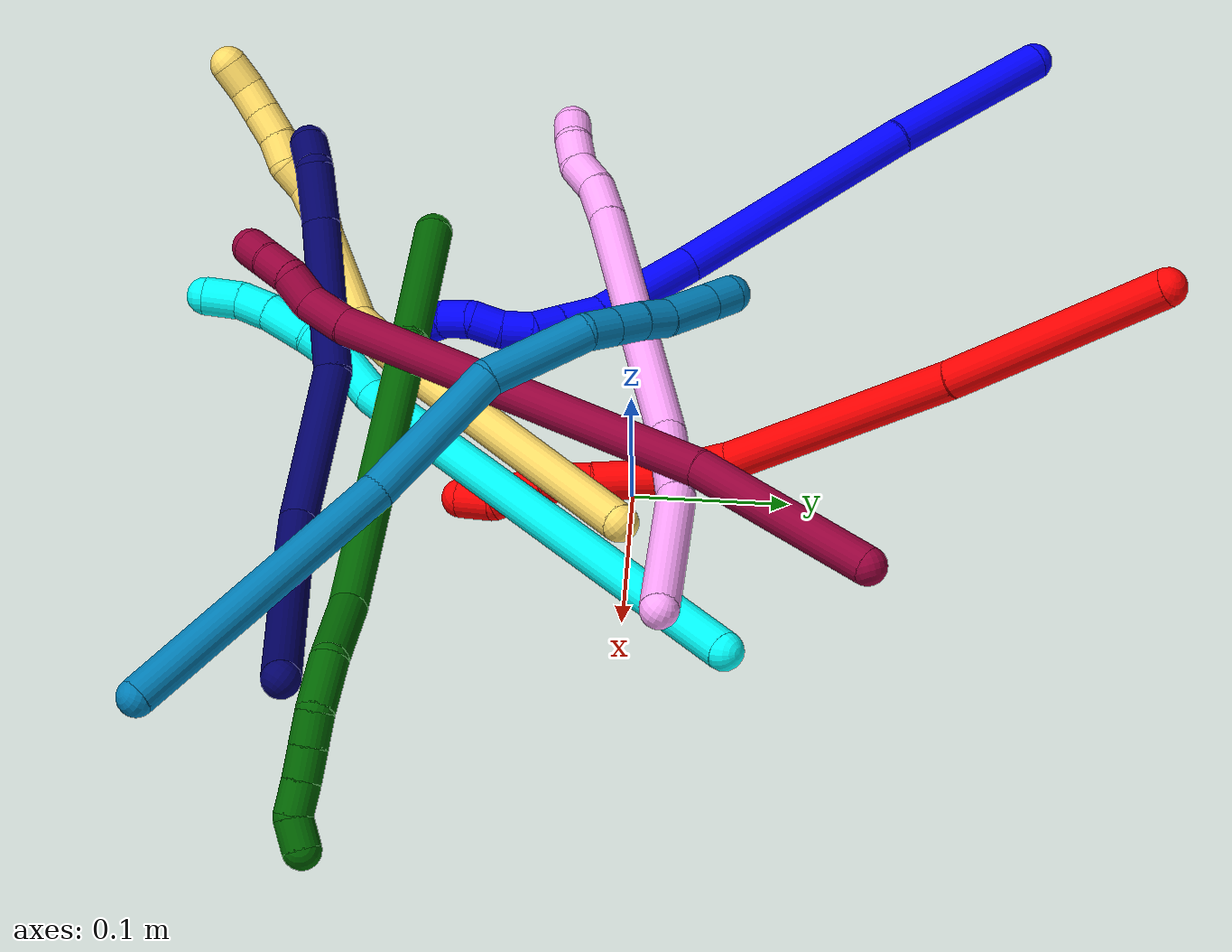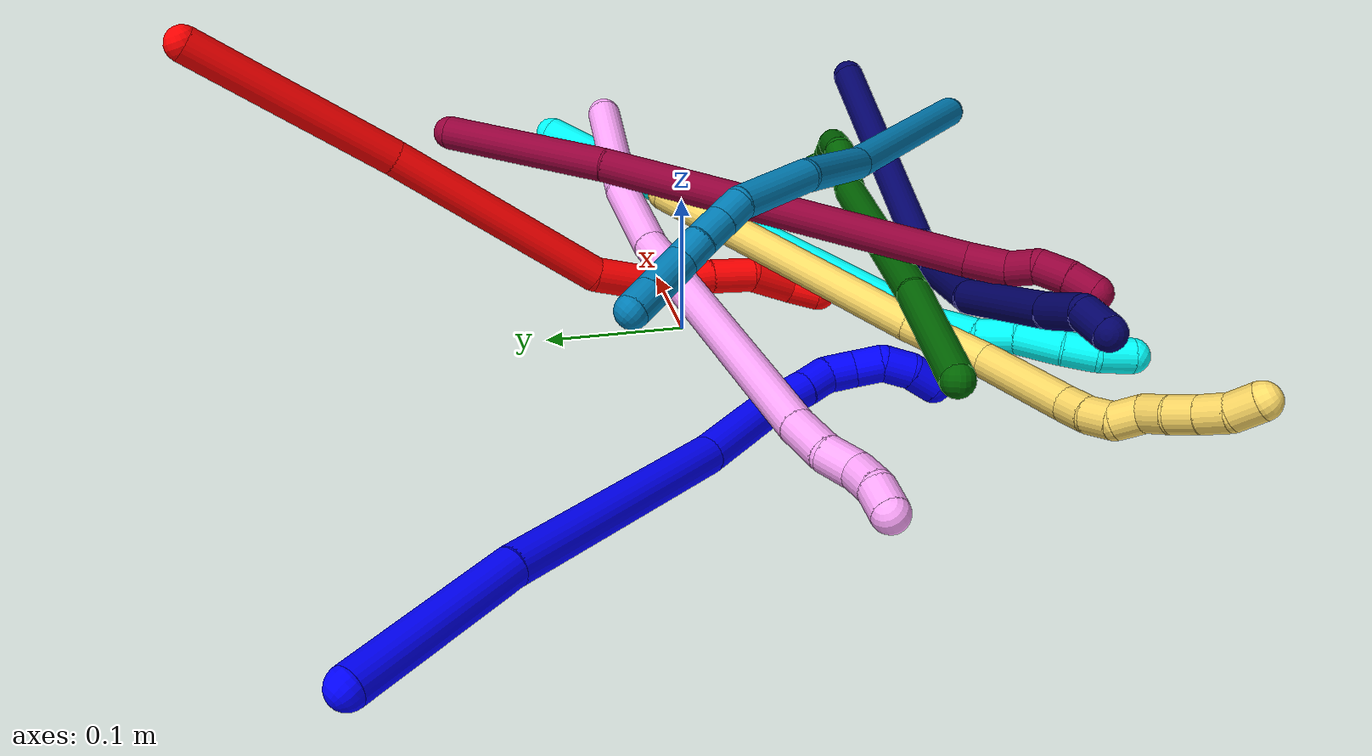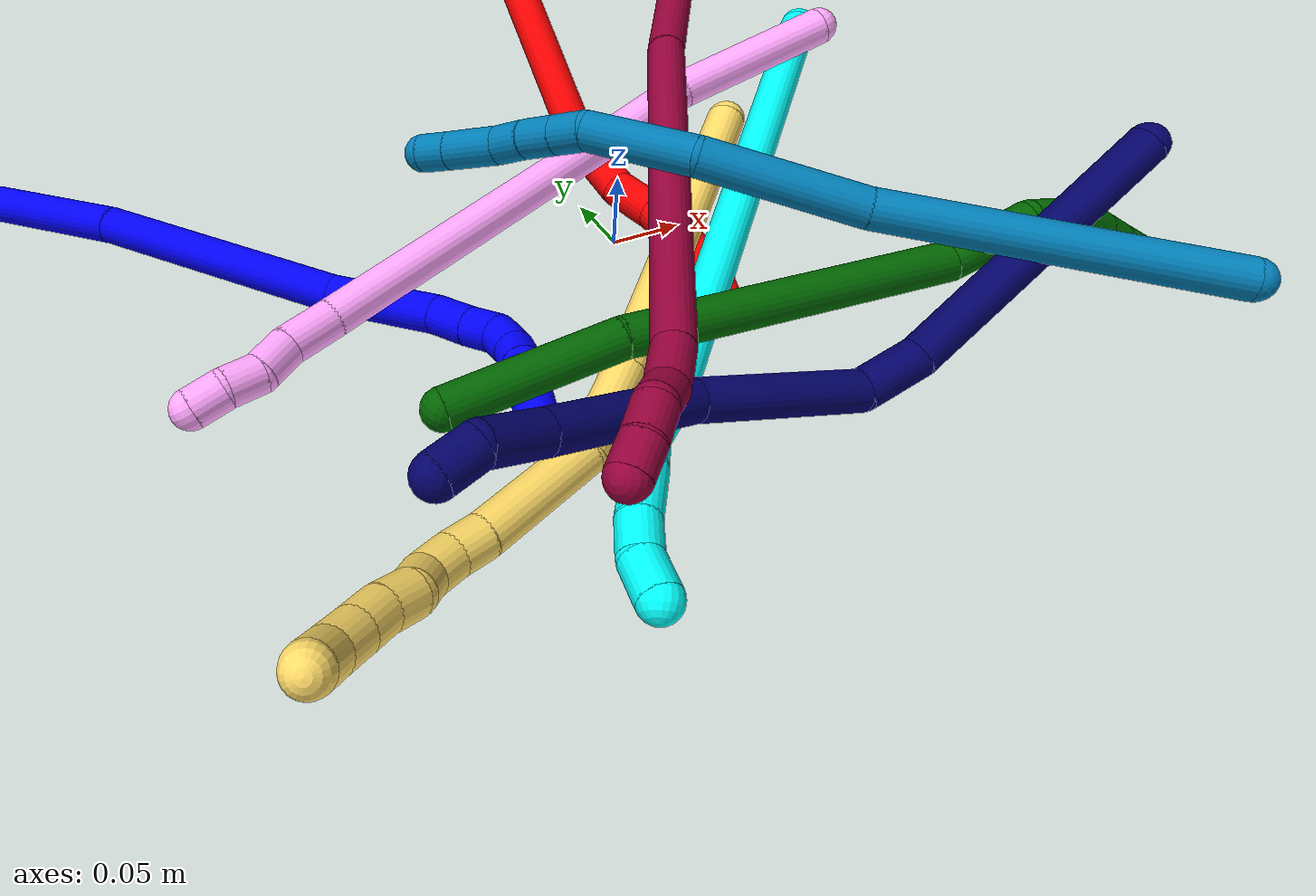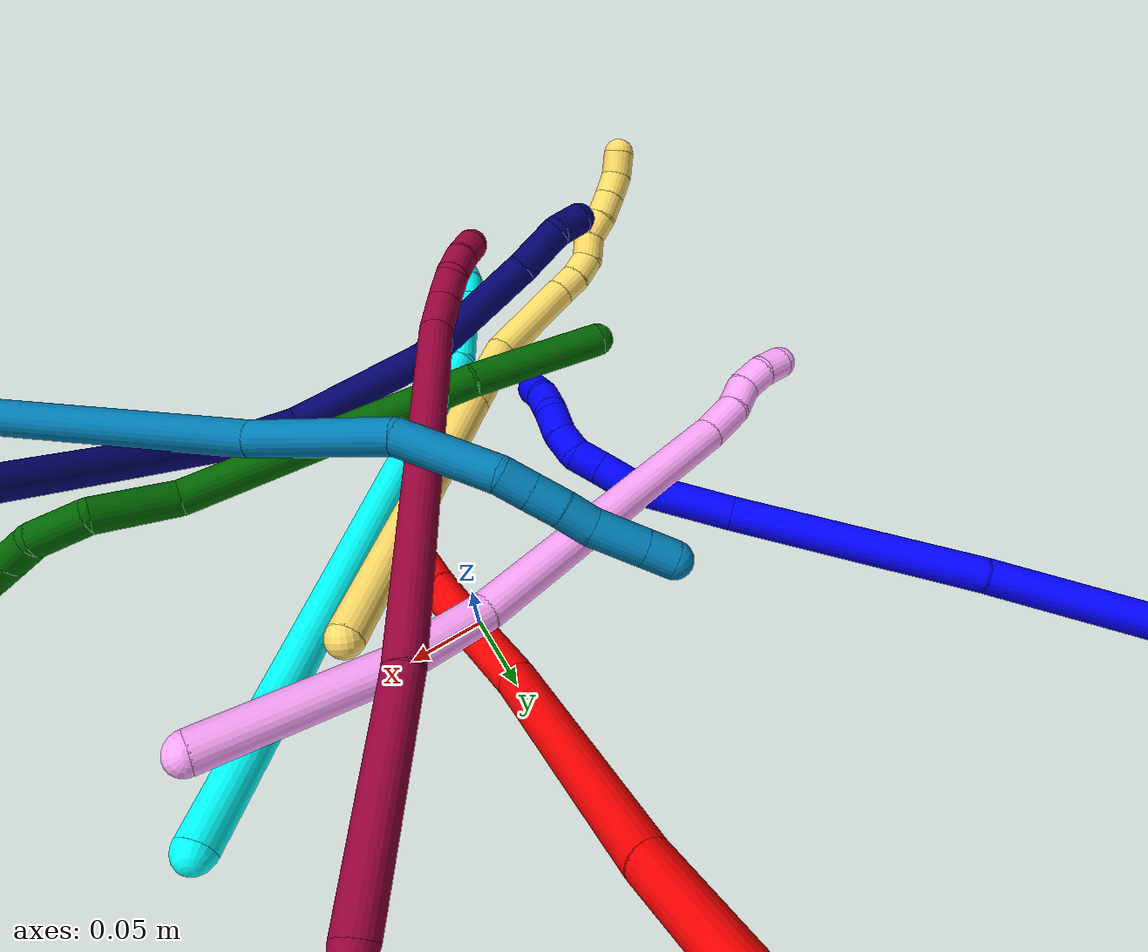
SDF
<sdf version="1.7">
 <world name="default">
  <plugin name="TubeGeneratorPlugin" filename="libtube_generator_plugin.so"/>
  <model name="photoneo_s_sensor">
   <static>1</static>
   <pose>0 0 2 1.57079 1.57079 3.14159</pose>
   <link name="link">
    <inertial><mass>0.1</mass></inertial>
    <sensor name="sensor" type="depth">
     <update_rate>30</update_rate>
     <camera>
      <horizontal_fov>1.22</horizontal_fov>
      <image><width>1920</width><height>1200</height><format>B8G8R8</format></image>
      <clip><near>0.1</near><far>4</far></clip>
      <depth_camera><output>points</output></depth_camera>
     </camera>
     <plugin name="camera_plugin" filename="libgazebo_ros_depth_camera.so">
      <baseline>0.2</baseline>
      <alwaysOn>1</alwaysOn>
      <updateRate>0.0</updateRate>
      <cameraName>camera_ir</cameraName>
      <imageTopicName>/camera/color/image_raw</imageTopicName>
      <cameraInfoTopicName>/camera/color/camera_info</cameraInfoTopicName>
      <depthImageTopicName>/camera/depth/image_raw</depthImageTopicName>
      <depthImageCameraInfoTopicName>/camera/depth/camera_info</depthImageCameraInfoTopicName>
      <pointCloudTopicName>/camera/depth/points</pointCloudTopicName>
      <frameName>fr_optical</frameName>
      <pointCloudCutoff>0.1</pointCloudCutoff>
      <pointCloudCutoffMax>2.0</pointCloudCutoffMax>
      <distortionK1>0</distortionK1>
      <distortionK2>0</distortionK2>
      <distortionK3>0</distortionK3>
      <distortionT1>0</distortionT1>
      <distortionT2>0</distortionT2>
      <CxPrime>0</CxPrime>
      <Cx>0</Cx>
      <Cy>0</Cy>
      <focalLength>0</focalLength>
      <hackBaseline>0</hackBaseline>
     </plugin>
    </sensor>
   </link>
  </model>
  <gravity>0 0 -9.8</gravity>
  <magnetic_field>6e-06 2.3e-05 -4.2e-05</magnetic_field>
  <atmosphere type="adiabatic"/>
  <physics name="default_physics" default="0" type="ode">
   <max_step_size>0.003</max_step_size>
   <real_time_factor>1</real_time_factor>
   <real_time_update_rate>1000</real_time_update_rate>
   <max_contacts>10000</max_contacts>
   <ode>
    <solver>
     <type>quick</type>
     <iters>100</iters>
     <sor>1.3</sor>
     <use_dynamic_moi_rescaling>0</use_dynamic_moi_rescaling>
    </solver>
    <constraints>
     <contact_max_correcting_vel>0</contact_max_correcting_vel>
     <contact_surface_layer>0.001</contact_surface_layer>
     <cfm>0</cfm>
     <erp>0.2</erp>
    </constraints>
   </ode>
  </physics>
  <scene><ambient>0.4 0.4 0.4 1</ambient><background>0.7 0.7 0.7 1</background><shadows>0</shadows></scene>
  <audio><device>default</device></audio>
  <spherical_coordinates>
   <surface_model>EARTH_WGS84</surface_model>
   <latitude_deg>0</latitude_deg>
   <longitude_deg>0</longitude_deg>
   <elevation>0</elevation>
   <heading_deg>0</heading_deg>
  </spherical_coordinates>
  <model name="bin">
   <static>1</static>
   <link name="bottom">
    <collision name="collision-bottom">
     <pose>0 0 -0.01 0 -0 0</pose>
     <geometry><box><size>0.8 0.6 0.02</size></box></geometry>
     <surface>
      <friction><ode><mu>100</mu><mu2>100</mu2></ode></friction>
      <contact><collide_bitmask>65535</collide_bitmask></contact>
     </surface>
    </collision>
   </link>
   <link name="west_wall">
    <collision name="collision-west_wall">
     <pose>-0.41 0 0.1 0 -0 0</pose>
     <geometry><box><size>0.02 0.6 0.2</size></box></geometry>
     <surface>
      <friction><ode><mu>100</mu><mu2>100</mu2></ode></friction>
      <contact><collide_bitmask>65535</collide_bitmask></contact>
     </surface>
    </collision>
   </link>
   <link name="east_wall">
    <collision name="collision-east_wall">
     <pose>0.41 0 0.1 0 -0 0</pose>
     <geometry><box><size>0.02 0.6 0.2</size></box></geometry>
     <surface>
      <friction><ode><mu>100</mu><mu2>100</mu2></ode></friction>
      <contact><collide_bitmask>65535</collide_bitmask></contact>
     </surface>
    </collision>
   </link>
   <link name="south_wall">
    <collision name="collision-south_wall">
     <pose>0 -0.31 0.1 0 -0 0</pose>
     <geometry><box><size>0.8 0.02 0.2</size></box></geometry>
     <surface>
      <friction><ode><mu>100</mu><mu2>100</mu2></ode></friction>
      <contact><collide_bitmask>65535</collide_bitmask></contact>
     </surface>
    </collision>
   </link>
   <link name="north_wall">
    <collision name="collision-north_wall">
     <pose>0 0.31 0.1 0 -0 0</pose>
     <geometry><box><size>0.8 0.02 0.2</size></box></geometry>
     <surface>
      <friction><ode><mu>100</mu><mu2>100</mu2></ode></friction>
      <contact><collide_bitmask>65535</collide_bitmask></contact>
     </surface>
    </collision>
   </link>
  </model>
  <model name="1">
   <static>0</static>
   <link name="1">
    <collision name="collision-cylinder-e_1_1_4">
     <pose>0.010332 -0.026176 -0.053137 2.68387 0.172684 0.711534</pose>
     <geometry><cylinder><radius>0.0125</radius><length>0.120258</length></cylinder></geometry>
     <surface>
      <friction><ode><mu>1.16</mu><mu2>1.16</mu2><slip1>0</slip1><slip2>0</slip2></ode></friction>
      <contact><ode><kp>1e+06</kp><kd>1</kd><max_vel>0</max_vel><min_depth>0.001</min_depth></ode></contact>
     </surface>
    </collision>
    <visual name="visual-cylinder-e_1_1_4">
     <pose>0.010332 -0.026176 -0.053137 2.68387 0.172684 0.711534</pose>
     <geometry><cylinder><radius>0.0125</radius><length>0.120258</length></cylinder></geometry>
     <material><ambient>0 0 1 1</ambient></material>
    </visual>
    <collision name="collision-cylinder-e_2_4_5">
     <pose>0.043731 -0.094124 -0.180618 2.62968 0.264189 0.939612</pose>
     <geometry><cylinder><radius>0.0125</radius><length>0.17668</length></cylinder></geometry>
     <surface>
      <friction><ode><mu>1.16</mu><mu2>1.16</mu2><slip1>0</slip1><slip2>0</slip2></ode></friction>
      <contact><ode><kp>1e+06</kp><kd>1</kd><max_vel>0</max_vel><min_depth>0.001</min_depth></ode></contact>
     </surface>
    </collision>
    <visual name="visual-cylinder-e_2_4_5">
     <pose>0.043731 -0.094124 -0.180618 2.62968 0.264189 0.939612</pose>
     <geometry><cylinder><radius>0.0125</radius><length>0.17668</length></cylinder></geometry>
     <material><ambient>0 0 1 1</ambient></material>
    </visual>
    <collision name="collision-cylinder-e_3_5_6">
     <pose>0.073075 -0.152246 -0.287504 2.67599 0.170642 0.692398</pose>
     <geometry><cylinder><radius>0.0125</radius><length>0.073912</length></cylinder></geometry>
     <surface>
      <friction><ode><mu>1.16</mu><mu2>1.16</mu2><slip1>0</slip1><slip2>0</slip2></ode></friction>
      <contact><ode><kp>1e+06</kp><kd>1</kd><max_vel>0</max_vel><min_depth>0.001</min_depth></ode></contact>
     </surface>
    </collision>
    <visual name="visual-cylinder-e_3_5_6">
     <pose>0.073075 -0.152246 -0.287504 2.67599 0.170642 0.692398</pose>
     <geometry><cylinder><radius>0.0125</radius><length>0.073912</length></cylinder></geometry>
     <material><ambient>0 0 1 1</ambient></material>
    </visual>
    <collision name="collision-cylinder-e_4_6_7">
     <pose>0.083442 -0.171438 -0.332986 2.92552 0.299568 1.89527</pose>
     <geometry><cylinder><radius>0.0125</radius><length>0.02773</length></cylinder></geometry>
     <surface>
      <friction><ode><mu>1.16</mu><mu2>1.16</mu2><slip1>0</slip1><slip2>0</slip2></ode></friction>
      <contact><ode><kp>1e+06</kp><kd>1</kd><max_vel>0</max_vel><min_depth>0.001</min_depth></ode></contact>
     </surface>
    </collision>
    <visual name="visual-cylinder-e_4_6_7">
     <pose>0.083442 -0.171438 -0.332986 2.92552 0.299568 1.89527</pose>
     <geometry><cylinder><radius>0.0125</radius><length>0.02773</length></cylinder></geometry>
     <material><ambient>0 0 1 1</ambient></material>
    </visual>
    <collision name="collision-cylinder-e_5_7_8">
     <pose>0.089874 -0.176512 -0.355925 2.92177 0.224481 1.59196</pose>
     <geometry><cylinder><radius>0.0125</radius><length>0.021021</length></cylinder></geometry>
     <surface>
      <friction><ode><mu>1.16</mu><mu2>1.16</mu2><slip1>0</slip1><slip2>0</slip2></ode></friction>
      <contact><ode><kp>1e+06</kp><kd>1</kd><max_vel>0</max_vel><min_depth>0.001</min_depth></ode></contact>
     </surface>
    </collision>
    <visual name="visual-cylinder-e_5_7_8">
     <pose>0.089874 -0.176512 -0.355925 2.92177 0.224481 1.59196</pose>
     <geometry><cylinder><radius>0.0125</radius><length>0.021021</length></cylinder></geometry>
     <material><ambient>0 0 1 1</ambient></material>
    </visual>
    <collision name="collision-cylinder-e_6_8_9">
     <pose>0.097422 -0.177469 -0.374538 -2.99431 0.539148 -2.61973</pose>
     <geometry><cylinder><radius>0.0125</radius><length>0.020291</length></cylinder></geometry>
     <surface>
      <friction><ode><mu>1.16</mu><mu2>1.16</mu2><slip1>0</slip1><slip2>0</slip2></ode></friction>
      <contact><ode><kp>1e+06</kp><kd>1</kd><max_vel>0</max_vel><min_depth>0.001</min_depth></ode></contact>
     </surface>
    </collision>
    <visual name="visual-cylinder-e_6_8_9">
     <pose>0.097422 -0.177469 -0.374538 -2.99431 0.539148 -2.61973</pose>
     <geometry><cylinder><radius>0.0125</radius><length>0.020291</length></cylinder></geometry>
     <material><ambient>0 0 1 1</ambient></material>
    </visual>
    <collision name="collision-cylinder-e_7_9_10">
     <pose>0.107612 -0.172292 -0.390943 -2.67765 0.519259 -1.68783</pose>
     <geometry><cylinder><radius>0.0125</radius><length>0.020074</length></cylinder></geometry>
     <surface>
      <friction><ode><mu>1.16</mu><mu2>1.16</mu2><slip1>0</slip1><slip2>0</slip2></ode></friction>
      <contact><ode><kp>1e+06</kp><kd>1</kd><max_vel>0</max_vel><min_depth>0.001</min_depth></ode></contact>
     </surface>
    </collision>
    <visual name="visual-cylinder-e_7_9_10">
     <pose>0.107612 -0.172292 -0.390943 -2.67765 0.519259 -1.68783</pose>
     <geometry><cylinder><radius>0.0125</radius><length>0.020074</length></cylinder></geometry>
     <material><ambient>0 0 1 1</ambient></material>
    </visual>
    <collision name="collision-cylinder-e_8_10_11">
     <pose>0.121041 -0.167146 -0.403945 -2.90668 1.00579 -2.71896</pose>
     <geometry><cylinder><radius>0.0125</radius><length>0.020007</length></cylinder></geometry>
     <surface>
      <friction><ode><mu>1.16</mu><mu2>1.16</mu2><slip1>0</slip1><slip2>0</slip2></ode></friction>
      <contact><ode><kp>1e+06</kp><kd>1</kd><max_vel>0</max_vel><min_depth>0.001</min_depth></ode></contact>
     </surface>
    </collision>
    <visual name="visual-cylinder-e_8_10_11">
     <pose>0.121041 -0.167146 -0.403945 -2.90668 1.00579 -2.71896</pose>
     <geometry><cylinder><radius>0.0125</radius><length>0.020007</length></cylinder></geometry>
     <material><ambient>0 0 1 1</ambient></material>
    </visual>
    <collision name="collision-cylinder-e_9_11_2">
     <pose>0.138778 -0.167239 -0.412647 2.77533 1.18789 2.60623</pose>
     <geometry><cylinder><radius>0.0125</radius><length>0.020026</length></cylinder></geometry>
     <surface>
      <friction><ode><mu>1.16</mu><mu2>1.16</mu2><slip1>0</slip1><slip2>0</slip2></ode></friction>
      <contact><ode><kp>1e+06</kp><kd>1</kd><max_vel>0</max_vel><min_depth>0.001</min_depth></ode></contact>
     </surface>
    </collision>
    <visual name="visual-cylinder-e_9_11_2">
     <pose>0.138778 -0.167239 -0.412647 2.77533 1.18789 2.60623</pose>
     <geometry><cylinder><radius>0.0125</radius><length>0.020026</length></cylinder></geometry>
     <material><ambient>0 0 1 1</ambient></material>
    </visual>
    <collision name="collision-sphere-2">
     <pose>0.148067 -0.168579 -0.41614 0 -0 0</pose>
     <geometry><sphere><radius>0.0125</radius></sphere></geometry>
     <surface>
      <friction><ode><mu>1.16</mu><mu2>1.16</mu2><slip1>0</slip1><slip2>0</slip2></ode></friction>
      <contact><ode><kp>1e+06</kp><kd>1</kd><max_vel>0</max_vel><min_depth>0.001</min_depth></ode></contact>
     </surface>
    </collision>
    <visual name="visual-sphere-2">
     <pose>0.148067 -0.168579 -0.41614 0 -0 0</pose>
     <geometry><sphere><radius>0.0125</radius></sphere></geometry>
     <material><ambient>0 0 1 1</ambient></material>
    </visual>
    <collision name="collision-sphere-11">
     <pose>0.12949 -0.165899 -0.409154 0 -0 0</pose>
     <geometry><sphere><radius>0.0125</radius></sphere></geometry>
     <surface>
      <friction><ode><mu>1.16</mu><mu2>1.16</mu2><slip1>0</slip1><slip2>0</slip2></ode></friction>
      <contact><ode><kp>1e+06</kp><kd>1</kd><max_vel>0</max_vel><min_depth>0.001</min_depth></ode></contact>
     </surface>
    </collision>
    <visual name="visual-sphere-11">
     <pose>0.12949 -0.165899 -0.409154 0 -0 0</pose>
     <geometry><sphere><radius>0.0125</radius></sphere></geometry>
     <material><ambient>0 0 1 1</ambient></material>
    </visual>
    <collision name="collision-sphere-10">
     <pose>0.112593 -0.168392 -0.398736 0 -0 0</pose>
     <geometry><sphere><radius>0.0125</radius></sphere></geometry>
     <surface>
      <friction><ode><mu>1.16</mu><mu2>1.16</mu2><slip1>0</slip1><slip2>0</slip2></ode></friction>
      <contact><ode><kp>1e+06</kp><kd>1</kd><max_vel>0</max_vel><min_depth>0.001</min_depth></ode></contact>
     </surface>
    </collision>
    <visual name="visual-sphere-10">
     <pose>0.112593 -0.168392 -0.398736 0 -0 0</pose>
     <geometry><sphere><radius>0.0125</radius></sphere></geometry>
     <material><ambient>0 0 1 1</ambient></material>
    </visual>
    <collision name="collision-sphere-9">
     <pose>0.102631 -0.176191 -0.38315 0 -0 0</pose>
     <geometry><sphere><radius>0.0125</radius></sphere></geometry>
     <surface>
      <friction><ode><mu>1.16</mu><mu2>1.16</mu2><slip1>0</slip1><slip2>0</slip2></ode></friction>
      <contact><ode><kp>1e+06</kp><kd>1</kd><max_vel>0</max_vel><min_depth>0.001</min_depth></ode></contact>
     </surface>
    </collision>
    <visual name="visual-sphere-9">
     <pose>0.102631 -0.176191 -0.38315 0 -0 0</pose>
     <geometry><sphere><radius>0.0125</radius></sphere></geometry>
     <material><ambient>0 0 1 1</ambient></material>
    </visual>
    <collision name="collision-sphere-4">
     <pose>0.020664 -0.052353 -0.106274 0 -0 0</pose>
     <geometry><sphere><radius>0.0125</radius></sphere></geometry>
     <surface>
      <friction><ode><mu>1.16</mu><mu2>1.16</mu2><slip1>0</slip1><slip2>0</slip2></ode></friction>
      <contact><ode><kp>1e+06</kp><kd>1</kd><max_vel>0</max_vel><min_depth>0.001</min_depth></ode></contact>
     </surface>
    </collision>
    <visual name="visual-sphere-4">
     <pose>0.020664 -0.052353 -0.106274 0 -0 0</pose>
     <geometry><sphere><radius>0.0125</radius></sphere></geometry>
     <material><ambient>0 0 1 1</ambient></material>
    </visual>
    <collision name="collision-sphere-1">
     <geometry><sphere><radius>0.0125</radius></sphere></geometry>
     <surface>
      <friction><ode><mu>1.16</mu><mu2>1.16</mu2><slip1>0</slip1><slip2>0</slip2></ode></friction>
      <contact><ode><kp>1e+06</kp><kd>1</kd><max_vel>0</max_vel><min_depth>0.001</min_depth></ode></contact>
     </surface>
    </collision>
    <visual name="visual-sphere-1">
     <geometry><sphere><radius>0.0125</radius></sphere></geometry>
     <material><ambient>0 0 1 1</ambient></material>
    </visual>
    <collision name="collision-sphere-8">
     <pose>0.092213 -0.178747 -0.365926 0 -0 0</pose>
     <geometry><sphere><radius>0.0125</radius></sphere></geometry>
     <surface>
      <friction><ode><mu>1.16</mu><mu2>1.16</mu2><slip1>0</slip1><slip2>0</slip2></ode></friction>
      <contact><ode><kp>1e+06</kp><kd>1</kd><max_vel>0</max_vel><min_depth>0.001</min_depth></ode></contact>
     </surface>
    </collision>
    <visual name="visual-sphere-8">
     <pose>0.092213 -0.178747 -0.365926 0 -0 0</pose>
     <geometry><sphere><radius>0.0125</radius></sphere></geometry>
     <material><ambient>0 0 1 1</ambient></material>
    </visual>
    <collision name="collision-sphere-5">
     <pose>0.066799 -0.135896 -0.254961 0 -0 0</pose>
     <geometry><sphere><radius>0.0125</radius></sphere></geometry>
     <surface>
      <friction><ode><mu>1.16</mu><mu2>1.16</mu2><slip1>0</slip1><slip2>0</slip2></ode></friction>
      <contact><ode><kp>1e+06</kp><kd>1</kd><max_vel>0</max_vel><min_depth>0.001</min_depth></ode></contact>
     </surface>
    </collision>
    <visual name="visual-sphere-5">
     <pose>0.066799 -0.135896 -0.254961 0 -0 0</pose>
     <geometry><sphere><radius>0.0125</radius></sphere></geometry>
     <material><ambient>0 0 1 1</ambient></material>
    </visual>
    <collision name="collision-sphere-6">
     <pose>0.079351 -0.168597 -0.320046 0 -0 0</pose>
     <geometry><sphere><radius>0.0125</radius></sphere></geometry>
     <surface>
      <friction><ode><mu>1.16</mu><mu2>1.16</mu2><slip1>0</slip1><slip2>0</slip2></ode></friction>
      <contact><ode><kp>1e+06</kp><kd>1</kd><max_vel>0</max_vel><min_depth>0.001</min_depth></ode></contact>
     </surface>
    </collision>
    <visual name="visual-sphere-6">
     <pose>0.079351 -0.168597 -0.320046 0 -0 0</pose>
     <geometry><sphere><radius>0.0125</radius></sphere></geometry>
     <material><ambient>0 0 1 1</ambient></material>
    </visual>
    <collision name="collision-sphere-7">
     <pose>0.087534 -0.174278 -0.345925 0 -0 0</pose>
     <geometry><sphere><radius>0.0125</radius></sphere></geometry>
     <surface>
      <friction><ode><mu>1.16</mu><mu2>1.16</mu2><slip1>0</slip1><slip2>0</slip2></ode></friction>
      <contact><ode><kp>1e+06</kp><kd>1</kd><max_vel>0</max_vel><min_depth>0.001</min_depth></ode></contact>
     </surface>
    </collision>
    <visual name="visual-sphere-7">
     <pose>0.087534 -0.174278 -0.345925 0 -0 0</pose>
     <geometry><sphere><radius>0.0125</radius></sphere></geometry>
     <material><ambient>0 0 1 1</ambient></material>
    </visual>
    <inertial>
     <pose>0.055822 -0.106496 -0.216121 0 -0 0</pose>
     <mass>0.5</mass>
     <inertia>
      <ixx>0.000898</ixx>
      <ixy>0</ixy>
      <ixz>0</ixz>
      <iyy>0.000168</iyy>
      <iyz>0</iyz>
      <izz>0.000111</izz>
     </inertia>
    </inertial>
   </link>
   <pose>-0.388409 0.247807 0.001604 2.29677 0.793264 -2.09991</pose>
  </model>
  <model name="2">
   <static>0</static>
   <link name="2">
    <collision name="collision-cylinder-e_1_1_4">
     <pose>0.014368 -0.043693 -0.062184 2.5291 0.186843 0.576149</pose>
     <geometry><cylinder><radius>0.0125</radius><length>0.154691</length></cylinder></geometry>
     <surface>
      <friction><ode><mu>1.16</mu><mu2>1.16</mu2><slip1>0</slip1><slip2>0</slip2></ode></friction>
      <contact><ode><kp>1e+06</kp><kd>1</kd><max_vel>0</max_vel><min_depth>0.001</min_depth></ode></contact>
     </surface>
    </collision>
    <visual name="visual-cylinder-e_1_1_4">
     <pose>0.014368 -0.043693 -0.062184 2.5291 0.186843 0.576149</pose>
     <geometry><cylinder><radius>0.0125</radius><length>0.154691</length></cylinder></geometry>
     <material><ambient>1 0 0 1</ambient></material>
    </visual>
    <collision name="collision-cylinder-e_2_4_5">
     <pose>0.038106 -0.134049 -0.192476 2.54091 0.113019 0.361326</pose>
     <geometry><cylinder><radius>0.0125</radius><length>0.166181</length></cylinder></geometry>
     <surface>
      <friction><ode><mu>1.16</mu><mu2>1.16</mu2><slip1>0</slip1><slip2>0</slip2></ode></friction>
      <contact><ode><kp>1e+06</kp><kd>1</kd><max_vel>0</max_vel><min_depth>0.001</min_depth></ode></contact>
     </surface>
    </collision>
    <visual name="visual-cylinder-e_2_4_5">
     <pose>0.038106 -0.134049 -0.192476 2.54091 0.113019 0.361326</pose>
     <geometry><cylinder><radius>0.0125</radius><length>0.166181</length></cylinder></geometry>
     <material><ambient>1 0 0 1</ambient></material>
    </visual>
    <collision name="collision-cylinder-e_3_5_6">
     <pose>0.053776 -0.20048 -0.27548 2.21658 0.249193 0.492226</pose>
     <geometry><cylinder><radius>0.0125</radius><length>0.051081</length></cylinder></geometry>
     <surface>
      <friction><ode><mu>1.16</mu><mu2>1.16</mu2><slip1>0</slip1><slip2>0</slip2></ode></friction>
      <contact><ode><kp>1e+06</kp><kd>1</kd><max_vel>0</max_vel><min_depth>0.001</min_depth></ode></contact>
     </surface>
    </collision>
    <visual name="visual-cylinder-e_3_5_6">
     <pose>0.053776 -0.20048 -0.27548 2.21658 0.249193 0.492226</pose>
     <geometry><cylinder><radius>0.0125</radius><length>0.051081</length></cylinder></geometry>
     <material><ambient>1 0 0 1</ambient></material>
    </visual>
    <collision name="collision-cylinder-e_4_6_7">
     <pose>0.065308 -0.238382 -0.296222 1.88264 0.268052 0.366119</pose>
     <geometry><cylinder><radius>0.0125</radius><length>0.039518</length></cylinder></geometry>
     <surface>
      <friction><ode><mu>1.16</mu><mu2>1.16</mu2><slip1>0</slip1><slip2>0</slip2></ode></friction>
      <contact><ode><kp>1e+06</kp><kd>1</kd><max_vel>0</max_vel><min_depth>0.001</min_depth></ode></contact>
     </surface>
    </collision>
    <visual name="visual-cylinder-e_4_6_7">
     <pose>0.065308 -0.238382 -0.296222 1.88264 0.268052 0.366119</pose>
     <geometry><cylinder><radius>0.0125</radius><length>0.039518</length></cylinder></geometry>
     <material><ambient>1 0 0 1</ambient></material>
    </visual>
    <collision name="collision-cylinder-e_5_7_8">
     <pose>0.073461 -0.270869 -0.30829 1.97982 0.184542 0.280083</pose>
     <geometry><cylinder><radius>0.0125</radius><length>0.031828</length></cylinder></geometry>
     <surface>
      <friction><ode><mu>1.16</mu><mu2>1.16</mu2><slip1>0</slip1><slip2>0</slip2></ode></friction>
      <contact><ode><kp>1e+06</kp><kd>1</kd><max_vel>0</max_vel><min_depth>0.001</min_depth></ode></contact>
     </surface>
    </collision>
    <visual name="visual-cylinder-e_5_7_8">
     <pose>0.073461 -0.270869 -0.30829 1.97982 0.184542 0.280083</pose>
     <geometry><cylinder><radius>0.0125</radius><length>0.031828</length></cylinder></geometry>
     <material><ambient>1 0 0 1</ambient></material>
    </visual>
    <collision name="collision-cylinder-e_6_8_9">
     <pose>0.081306 -0.296788 -0.325903 2.34865 0.294543 0.681092</pose>
     <geometry><cylinder><radius>0.0125</radius><length>0.033929</length></cylinder></geometry>
     <surface>
      <friction><ode><mu>1.16</mu><mu2>1.16</mu2><slip1>0</slip1><slip2>0</slip2></ode></friction>
      <contact><ode><kp>1e+06</kp><kd>1</kd><max_vel>0</max_vel><min_depth>0.001</min_depth></ode></contact>
     </surface>
    </collision>
    <visual name="visual-cylinder-e_6_8_9">
     <pose>0.081306 -0.296788 -0.325903 2.34865 0.294543 0.681092</pose>
     <geometry><cylinder><radius>0.0125</radius><length>0.033929</length></cylinder></geometry>
     <material><ambient>1 0 0 1</ambient></material>
    </visual>
    <collision name="collision-cylinder-e_7_9_2">
     <pose>0.084945 -0.31765 -0.343743 2.17712 -0.11316 -0.21557</pose>
     <geometry><cylinder><radius>0.0125</radius><length>0.022773</length></cylinder></geometry>
     <surface>
      <friction><ode><mu>1.16</mu><mu2>1.16</mu2><slip1>0</slip1><slip2>0</slip2></ode></friction>
      <contact><ode><kp>1e+06</kp><kd>1</kd><max_vel>0</max_vel><min_depth>0.001</min_depth></ode></contact>
     </surface>
    </collision>
    <visual name="visual-cylinder-e_7_9_2">
     <pose>0.084945 -0.31765 -0.343743 2.17712 -0.11316 -0.21557</pose>
     <geometry><cylinder><radius>0.0125</radius><length>0.022773</length></cylinder></geometry>
     <material><ambient>1 0 0 1</ambient></material>
    </visual>
    <collision name="collision-sphere-2">
     <pose>0.083659 -0.326947 -0.35019 0 -0 0</pose>
     <geometry><sphere><radius>0.0125</radius></sphere></geometry>
     <surface>
      <friction><ode><mu>1.16</mu><mu2>1.16</mu2><slip1>0</slip1><slip2>0</slip2></ode></friction>
      <contact><ode><kp>1e+06</kp><kd>1</kd><max_vel>0</max_vel><min_depth>0.001</min_depth></ode></contact>
     </surface>
    </collision>
    <visual name="visual-sphere-2">
     <pose>0.083659 -0.326947 -0.35019 0 -0 0</pose>
     <geometry><sphere><radius>0.0125</radius></sphere></geometry>
     <material><ambient>1 0 0 1</ambient></material>
    </visual>
    <collision name="collision-sphere-9">
     <pose>0.086231 -0.308353 -0.337296 0 -0 0</pose>
     <geometry><sphere><radius>0.0125</radius></sphere></geometry>
     <surface>
      <friction><ode><mu>1.16</mu><mu2>1.16</mu2><slip1>0</slip1><slip2>0</slip2></ode></friction>
      <contact><ode><kp>1e+06</kp><kd>1</kd><max_vel>0</max_vel><min_depth>0.001</min_depth></ode></contact>
     </surface>
    </collision>
    <visual name="visual-sphere-9">
     <pose>0.086231 -0.308353 -0.337296 0 -0 0</pose>
     <geometry><sphere><radius>0.0125</radius></sphere></geometry>
     <material><ambient>1 0 0 1</ambient></material>
    </visual>
    <collision name="collision-sphere-4">
     <pose>0.028735 -0.087386 -0.124368 0 -0 0</pose>
     <geometry><sphere><radius>0.0125</radius></sphere></geometry>
     <surface>
      <friction><ode><mu>1.16</mu><mu2>1.16</mu2><slip1>0</slip1><slip2>0</slip2></ode></friction>
      <contact><ode><kp>1e+06</kp><kd>1</kd><max_vel>0</max_vel><min_depth>0.001</min_depth></ode></contact>
     </surface>
    </collision>
    <visual name="visual-sphere-4">
     <pose>0.028735 -0.087386 -0.124368 0 -0 0</pose>
     <geometry><sphere><radius>0.0125</radius></sphere></geometry>
     <material><ambient>1 0 0 1</ambient></material>
    </visual>
    <collision name="collision-sphere-1">
     <geometry><sphere><radius>0.0125</radius></sphere></geometry>
     <surface>
      <friction><ode><mu>1.16</mu><mu2>1.16</mu2><slip1>0</slip1><slip2>0</slip2></ode></friction>
      <contact><ode><kp>1e+06</kp><kd>1</kd><max_vel>0</max_vel><min_depth>0.001</min_depth></ode></contact>
     </surface>
    </collision>
    <visual name="visual-sphere-1">
     <geometry><sphere><radius>0.0125</radius></sphere></geometry>
     <material><ambient>1 0 0 1</ambient></material>
    </visual>
    <collision name="collision-sphere-8">
     <pose>0.076381 -0.285223 -0.314511 0 -0 0</pose>
     <geometry><sphere><radius>0.0125</radius></sphere></geometry>
     <surface>
      <friction><ode><mu>1.16</mu><mu2>1.16</mu2><slip1>0</slip1><slip2>0</slip2></ode></friction>
      <contact><ode><kp>1e+06</kp><kd>1</kd><max_vel>0</max_vel><min_depth>0.001</min_depth></ode></contact>
     </surface>
    </collision>
    <visual name="visual-sphere-8">
     <pose>0.076381 -0.285223 -0.314511 0 -0 0</pose>
     <geometry><sphere><radius>0.0125</radius></sphere></geometry>
     <material><ambient>1 0 0 1</ambient></material>
    </visual>
    <collision name="collision-sphere-5">
     <pose>0.047477 -0.180713 -0.260584 0 -0 0</pose>
     <geometry><sphere><radius>0.0125</radius></sphere></geometry>
     <surface>
      <friction><ode><mu>1.16</mu><mu2>1.16</mu2><slip1>0</slip1><slip2>0</slip2></ode></friction>
      <contact><ode><kp>1e+06</kp><kd>1</kd><max_vel>0</max_vel><min_depth>0.001</min_depth></ode></contact>
     </surface>
    </collision>
    <visual name="visual-sphere-5">
     <pose>0.047477 -0.180713 -0.260584 0 -0 0</pose>
     <geometry><sphere><radius>0.0125</radius></sphere></geometry>
     <material><ambient>1 0 0 1</ambient></material>
    </visual>
    <collision name="collision-sphere-6">
     <pose>0.060074 -0.220248 -0.290376 0 -0 0</pose>
     <geometry><sphere><radius>0.0125</radius></sphere></geometry>
     <surface>
      <friction><ode><mu>1.16</mu><mu2>1.16</mu2><slip1>0</slip1><slip2>0</slip2></ode></friction>
      <contact><ode><kp>1e+06</kp><kd>1</kd><max_vel>0</max_vel><min_depth>0.001</min_depth></ode></contact>
     </surface>
    </collision>
    <visual name="visual-sphere-6">
     <pose>0.060074 -0.220248 -0.290376 0 -0 0</pose>
     <geometry><sphere><radius>0.0125</radius></sphere></geometry>
     <material><ambient>1 0 0 1</ambient></material>
    </visual>
    <collision name="collision-sphere-7">
     <pose>0.070541 -0.256516 -0.302068 0 -0 0</pose>
     <geometry><sphere><radius>0.0125</radius></sphere></geometry>
     <surface>
      <friction><ode><mu>1.16</mu><mu2>1.16</mu2><slip1>0</slip1><slip2>0</slip2></ode></friction>
      <contact><ode><kp>1e+06</kp><kd>1</kd><max_vel>0</max_vel><min_depth>0.001</min_depth></ode></contact>
     </surface>
    </collision>
    <visual name="visual-sphere-7">
     <pose>0.070541 -0.256516 -0.302068 0 -0 0</pose>
     <geometry><sphere><radius>0.0125</radius></sphere></geometry>
     <material><ambient>1 0 0 1</ambient></material>
    </visual>
    <inertial>
     <pose>0.041828 -0.149242 -0.192161 0 -0 0</pose>
     <mass>0.5</mass>
     <inertia>
      <ixx>0.00097</ixx>
      <ixy>0</ixy>
      <ixz>0</ixz>
      <iyy>-0.000209</iyy>
      <iyz>0</iyz>
      <izz>0.000284</izz>
     </inertia>
    </inertial>
   </link>
   <pose>-0.001557 0.325352 0.231564 -0.351773 0.051142 -0.125463</pose>
  </model>
  <model name="3">
   <static>0</static>
   <link name="3">
    <collision name="collision-cylinder-e_1_1_4">
     <pose>-0.037752 -0.043192 -0.168126 2.89013 -0.214148 -1.4094</pose>
     <geometry><cylinder><radius>0.0125</radius><length>0.355287</length></cylinder></geometry>
     <surface>
      <friction><ode><mu>1.16</mu><mu2>1.16</mu2><slip1>0</slip1><slip2>0</slip2></ode></friction>
      <contact><ode><kp>1e+06</kp><kd>1</kd><max_vel>0</max_vel><min_depth>0.001</min_depth></ode></contact>
     </surface>
    </collision>
    <visual name="visual-cylinder-e_1_1_4">
     <pose>-0.037752 -0.043192 -0.168126 2.89013 -0.214148 -1.4094</pose>
     <geometry><cylinder><radius>0.0125</radius><length>0.355287</length></cylinder></geometry>
     <material><ambient>0.003922 1 0.996078 1</ambient></material>
    </visual>
    <collision name="collision-cylinder-e_2_4_5">
     <pose>-0.080118 -0.095655 -0.351369 2.59151 -0.254588 -0.851583</pose>
     <geometry><cylinder><radius>0.0125</radius><length>0.036646</length></cylinder></geometry>
     <surface>
      <friction><ode><mu>1.16</mu><mu2>1.16</mu2><slip1>0</slip1><slip2>0</slip2></ode></friction>
      <contact><ode><kp>1e+06</kp><kd>1</kd><max_vel>0</max_vel><min_depth>0.001</min_depth></ode></contact>
     </surface>
    </collision>
    <visual name="visual-cylinder-e_2_4_5">
     <pose>-0.080118 -0.095655 -0.351369 2.59151 -0.254588 -0.851583</pose>
     <geometry><cylinder><radius>0.0125</radius><length>0.036646</length></cylinder></geometry>
     <material><ambient>0.003922 1 0.996078 1</ambient></material>
    </visual>
    <collision name="collision-cylinder-e_3_5_6">
     <pose>-0.083504 -0.112171 -0.377684 2.56723 0.091865 0.308787</pose>
     <geometry><cylinder><radius>0.0125</radius><length>0.02679</length></cylinder></geometry>
     <surface>
      <friction><ode><mu>1.16</mu><mu2>1.16</mu2><slip1>0</slip1><slip2>0</slip2></ode></friction>
      <contact><ode><kp>1e+06</kp><kd>1</kd><max_vel>0</max_vel><min_depth>0.001</min_depth></ode></contact>
     </surface>
    </collision>
    <visual name="visual-cylinder-e_3_5_6">
     <pose>-0.083504 -0.112171 -0.377684 2.56723 0.091865 0.308787</pose>
     <geometry><cylinder><radius>0.0125</radius><length>0.02679</length></cylinder></geometry>
     <material><ambient>0.003922 1 0.996078 1</ambient></material>
    </visual>
    <collision name="collision-cylinder-e_4_6_7">
     <pose>-0.082581 -0.125444 -0.404382 2.7708 -0.018375 -0.0979</pose>
     <geometry><cylinder><radius>0.0125</radius><length>0.033266</length></cylinder></geometry>
     <surface>
      <friction><ode><mu>1.16</mu><mu2>1.16</mu2><slip1>0</slip1><slip2>0</slip2></ode></friction>
      <contact><ode><kp>1e+06</kp><kd>1</kd><max_vel>0</max_vel><min_depth>0.001</min_depth></ode></contact>
     </surface>
    </collision>
    <visual name="visual-cylinder-e_4_6_7">
     <pose>-0.082581 -0.125444 -0.404382 2.7708 -0.018375 -0.0979</pose>
     <geometry><cylinder><radius>0.0125</radius><length>0.033266</length></cylinder></geometry>
     <material><ambient>0.003922 1 0.996078 1</ambient></material>
    </visual>
    <collision name="collision-cylinder-e_5_7_8">
     <pose>-0.081372 -0.135155 -0.430953 2.82029 0.129124 0.759239</pose>
     <geometry><cylinder><radius>0.0125</radius><length>0.023531</length></cylinder></geometry>
     <surface>
      <friction><ode><mu>1.16</mu><mu2>1.16</mu2><slip1>0</slip1><slip2>0</slip2></ode></friction>
      <contact><ode><kp>1e+06</kp><kd>1</kd><max_vel>0</max_vel><min_depth>0.001</min_depth></ode></contact>
     </surface>
    </collision>
    <visual name="visual-cylinder-e_5_7_8">
     <pose>-0.081372 -0.135155 -0.430953 2.82029 0.129124 0.759239</pose>
     <geometry><cylinder><radius>0.0125</radius><length>0.023531</length></cylinder></geometry>
     <material><ambient>0.003922 1 0.996078 1</ambient></material>
    </visual>
    <collision name="collision-cylinder-e_6_8_2">
     <pose>-0.074537 -0.14179 -0.452644 2.87062 0.449637 2.06648</pose>
     <geometry><cylinder><radius>0.0125</radius><length>0.024479</length></cylinder></geometry>
     <surface>
      <friction><ode><mu>1.16</mu><mu2>1.16</mu2><slip1>0</slip1><slip2>0</slip2></ode></friction>
      <contact><ode><kp>1e+06</kp><kd>1</kd><max_vel>0</max_vel><min_depth>0.001</min_depth></ode></contact>
     </surface>
    </collision>
    <visual name="visual-cylinder-e_6_8_2">
     <pose>-0.074537 -0.14179 -0.452644 2.87062 0.449637 2.06648</pose>
     <geometry><cylinder><radius>0.0125</radius><length>0.024479</length></cylinder></geometry>
     <material><ambient>0.003922 1 0.996078 1</ambient></material>
    </visual>
    <collision name="collision-sphere-2">
     <pose>-0.069217 -0.144741 -0.463265 0 -0 0</pose>
     <geometry><sphere><radius>0.0125</radius></sphere></geometry>
     <surface>
      <friction><ode><mu>1.16</mu><mu2>1.16</mu2><slip1>0</slip1><slip2>0</slip2></ode></friction>
      <contact><ode><kp>1e+06</kp><kd>1</kd><max_vel>0</max_vel><min_depth>0.001</min_depth></ode></contact>
     </surface>
    </collision>
    <visual name="visual-sphere-2">
     <pose>-0.069217 -0.144741 -0.463265 0 -0 0</pose>
     <geometry><sphere><radius>0.0125</radius></sphere></geometry>
     <material><ambient>0.003922 1 0.996078 1</ambient></material>
    </visual>
    <collision name="collision-sphere-4">
     <pose>-0.075504 -0.086385 -0.336252 0 -0 0</pose>
     <geometry><sphere><radius>0.0125</radius></sphere></geometry>
     <surface>
      <friction><ode><mu>1.16</mu><mu2>1.16</mu2><slip1>0</slip1><slip2>0</slip2></ode></friction>
      <contact><ode><kp>1e+06</kp><kd>1</kd><max_vel>0</max_vel><min_depth>0.001</min_depth></ode></contact>
     </surface>
    </collision>
    <visual name="visual-sphere-4">
     <pose>-0.075504 -0.086385 -0.336252 0 -0 0</pose>
     <geometry><sphere><radius>0.0125</radius></sphere></geometry>
     <material><ambient>0.003922 1 0.996078 1</ambient></material>
    </visual>
    <collision name="collision-sphere-1">
     <geometry><sphere><radius>0.0125</radius></sphere></geometry>
     <surface>
      <friction><ode><mu>1.16</mu><mu2>1.16</mu2><slip1>0</slip1><slip2>0</slip2></ode></friction>
      <contact><ode><kp>1e+06</kp><kd>1</kd><max_vel>0</max_vel><min_depth>0.001</min_depth></ode></contact>
     </surface>
    </collision>
    <visual name="visual-sphere-1">
     <geometry><sphere><radius>0.0125</radius></sphere></geometry>
     <material><ambient>0.003922 1 0.996078 1</ambient></material>
    </visual>
    <collision name="collision-sphere-8">
     <pose>-0.079856 -0.13884 -0.442024 0 -0 0</pose>
     <geometry><sphere><radius>0.0125</radius></sphere></geometry>
     <surface>
      <friction><ode><mu>1.16</mu><mu2>1.16</mu2><slip1>0</slip1><slip2>0</slip2></ode></friction>
      <contact><ode><kp>1e+06</kp><kd>1</kd><max_vel>0</max_vel><min_depth>0.001</min_depth></ode></contact>
     </surface>
    </collision>
    <visual name="visual-sphere-8">
     <pose>-0.079856 -0.13884 -0.442024 0 -0 0</pose>
     <geometry><sphere><radius>0.0125</radius></sphere></geometry>
     <material><ambient>0.003922 1 0.996078 1</ambient></material>
    </visual>
    <collision name="collision-sphere-5">
     <pose>-0.084733 -0.104925 -0.366486 0 -0 0</pose>
     <geometry><sphere><radius>0.0125</radius></sphere></geometry>
     <surface>
      <friction><ode><mu>1.16</mu><mu2>1.16</mu2><slip1>0</slip1><slip2>0</slip2></ode></friction>
      <contact><ode><kp>1e+06</kp><kd>1</kd><max_vel>0</max_vel><min_depth>0.001</min_depth></ode></contact>
     </surface>
    </collision>
    <visual name="visual-sphere-5">
     <pose>-0.084733 -0.104925 -0.366486 0 -0 0</pose>
     <geometry><sphere><radius>0.0125</radius></sphere></geometry>
     <material><ambient>0.003922 1 0.996078 1</ambient></material>
    </visual>
    <collision name="collision-sphere-6">
     <pose>-0.082275 -0.119418 -0.388882 0 -0 0</pose>
     <geometry><sphere><radius>0.0125</radius></sphere></geometry>
     <surface>
      <friction><ode><mu>1.16</mu><mu2>1.16</mu2><slip1>0</slip1><slip2>0</slip2></ode></friction>
      <contact><ode><kp>1e+06</kp><kd>1</kd><max_vel>0</max_vel><min_depth>0.001</min_depth></ode></contact>
     </surface>
    </collision>
    <visual name="visual-sphere-6">
     <pose>-0.082275 -0.119418 -0.388882 0 -0 0</pose>
     <geometry><sphere><radius>0.0125</radius></sphere></geometry>
     <material><ambient>0.003922 1 0.996078 1</ambient></material>
    </visual>
    <collision name="collision-sphere-7">
     <pose>-0.082887 -0.13147 -0.419882 0 -0 0</pose>
     <geometry><sphere><radius>0.0125</radius></sphere></geometry>
     <surface>
      <friction><ode><mu>1.16</mu><mu2>1.16</mu2><slip1>0</slip1><slip2>0</slip2></ode></friction>
      <contact><ode><kp>1e+06</kp><kd>1</kd><max_vel>0</max_vel><min_depth>0.001</min_depth></ode></contact>
     </surface>
    </collision>
    <visual name="visual-sphere-7">
     <pose>-0.082887 -0.13147 -0.419882 0 -0 0</pose>
     <geometry><sphere><radius>0.0125</radius></sphere></geometry>
     <material><ambient>0.003922 1 0.996078 1</ambient></material>
    </visual>
    <inertial>
     <pose>-0.050145 -0.065361 -0.234802 0 -0 0</pose>
     <mass>0.5</mass>
     <inertia>
      <ixx>-0.003024</ixx>
      <ixy>0</ixy>
      <ixz>0</ixz>
      <iyy>-0.004027</iyy>
      <iyz>0</iyz>
      <izz>0.00168</izz>
     </inertia>
    </inertial>
   </link>
   <pose>0.187934 0.068357 0.09581 -1.12445 -0.220109 -0.631286</pose>
  </model>
  <model name="4">
   <static>0</static>
   <link name="4">
    <collision name="collision-cylinder-e_1_1_4">
     <pose>-0.054612 -0.006445 0.005133 0.898232 -1.42105 -0.786235</pose>
     <geometry><cylinder><radius>0.0125</radius><length>0.110461</length></cylinder></geometry>
     <surface>
      <friction><ode><mu>1.16</mu><mu2>1.16</mu2><slip1>0</slip1><slip2>0</slip2></ode></friction>
      <contact><ode><kp>1e+06</kp><kd>1</kd><max_vel>0</max_vel><min_depth>0.001</min_depth></ode></contact>
     </surface>
    </collision>
    <visual name="visual-cylinder-e_1_1_4">
     <pose>-0.054612 -0.006445 0.005133 0.898232 -1.42105 -0.786235</pose>
     <geometry><cylinder><radius>0.0125</radius><length>0.110461</length></cylinder></geometry>
     <material><ambient>1 0.65098 0.996078 1</ambient></material>
    </visual>
    <collision name="collision-cylinder-e_2_4_5">
     <pose>-0.141984 -0.02128 0.00933 1.68197 -1.3186 -1.42778</pose>
     <geometry><cylinder><radius>0.0125</radius><length>0.067659</length></cylinder></geometry>
     <surface>
      <friction><ode><mu>1.16</mu><mu2>1.16</mu2><slip1>0</slip1><slip2>0</slip2></ode></friction>
      <contact><ode><kp>1e+06</kp><kd>1</kd><max_vel>0</max_vel><min_depth>0.001</min_depth></ode></contact>
     </surface>
    </collision>
    <visual name="visual-cylinder-e_2_4_5">
     <pose>-0.141984 -0.02128 0.00933 1.68197 -1.3186 -1.42778</pose>
     <geometry><cylinder><radius>0.0125</radius><length>0.067659</length></cylinder></geometry>
     <material><ambient>1 0.65098 0.996078 1</ambient></material>
    </visual>
    <collision name="collision-cylinder-e_3_5_6">
     <pose>-0.277369 -0.071227 0.010292 1.52515 -1.18566 -1.14372</pose>
     <geometry><cylinder><radius>0.0125</radius><length>0.221473</length></cylinder></geometry>
     <surface>
      <friction><ode><mu>1.16</mu><mu2>1.16</mu2><slip1>0</slip1><slip2>0</slip2></ode></friction>
      <contact><ode><kp>1e+06</kp><kd>1</kd><max_vel>0</max_vel><min_depth>0.001</min_depth></ode></contact>
     </surface>
    </collision>
    <visual name="visual-cylinder-e_3_5_6">
     <pose>-0.277369 -0.071227 0.010292 1.52515 -1.18566 -1.14372</pose>
     <geometry><cylinder><radius>0.0125</radius><length>0.221473</length></cylinder></geometry>
     <material><ambient>1 0.65098 0.996078 1</ambient></material>
    </visual>
    <collision name="collision-cylinder-e_4_6_7">
     <pose>-0.394499 -0.120314 0.013057 1.45617 -1.08939 -0.990395</pose>
     <geometry><cylinder><radius>0.0125</radius><length>0.032731</length></cylinder></geometry>
     <surface>
      <friction><ode><mu>1.16</mu><mu2>1.16</mu2><slip1>0</slip1><slip2>0</slip2></ode></friction>
      <contact><ode><kp>1e+06</kp><kd>1</kd><max_vel>0</max_vel><min_depth>0.001</min_depth></ode></contact>
     </surface>
    </collision>
    <visual name="visual-cylinder-e_4_6_7">
     <pose>-0.394499 -0.120314 0.013057 1.45617 -1.08939 -0.990395</pose>
     <geometry><cylinder><radius>0.0125</radius><length>0.032731</length></cylinder></geometry>
     <material><ambient>1 0.65098 0.996078 1</ambient></material>
    </visual>
    <collision name="collision-cylinder-e_5_7_8">
     <pose>-0.418182 -0.135916 0.012748 1.71537 -0.843999 -0.957577</pose>
     <geometry><cylinder><radius>0.0125</radius><length>0.024559</length></cylinder></geometry>
     <surface>
      <friction><ode><mu>1.16</mu><mu2>1.16</mu2><slip1>0</slip1><slip2>0</slip2></ode></friction>
      <contact><ode><kp>1e+06</kp><kd>1</kd><max_vel>0</max_vel><min_depth>0.001</min_depth></ode></contact>
     </surface>
    </collision>
    <visual name="visual-cylinder-e_5_7_8">
     <pose>-0.418182 -0.135916 0.012748 1.71537 -0.843999 -0.957577</pose>
     <geometry><cylinder><radius>0.0125</radius><length>0.024559</length></cylinder></geometry>
     <material><ambient>1 0.65098 0.996078 1</ambient></material>
    </visual>
    <collision name="collision-cylinder-e_6_8_9">
     <pose>-0.437125 -0.148836 0.013787 1.14204 -1.07146 -0.728664</pose>
     <geometry><cylinder><radius>0.0125</radius><length>0.022251</length></cylinder></geometry>
     <surface>
      <friction><ode><mu>1.16</mu><mu2>1.16</mu2><slip1>0</slip1><slip2>0</slip2></ode></friction>
      <contact><ode><kp>1e+06</kp><kd>1</kd><max_vel>0</max_vel><min_depth>0.001</min_depth></ode></contact>
     </surface>
    </collision>
    <visual name="visual-cylinder-e_6_8_9">
     <pose>-0.437125 -0.148836 0.013787 1.14204 -1.07146 -0.728664</pose>
     <geometry><cylinder><radius>0.0125</radius><length>0.022251</length></cylinder></geometry>
     <material><ambient>1 0.65098 0.996078 1</ambient></material>
    </visual>
    <collision name="collision-cylinder-e_7_9_2">
     <pose>-0.457033 -0.156124 0.016206 1.48749 -1.33355 -1.25336</pose>
     <geometry><cylinder><radius>0.0125</radius><length>0.020865</length></cylinder></geometry>
     <surface>
      <friction><ode><mu>1.16</mu><mu2>1.16</mu2><slip1>0</slip1><slip2>0</slip2></ode></friction>
      <contact><ode><kp>1e+06</kp><kd>1</kd><max_vel>0</max_vel><min_depth>0.001</min_depth></ode></contact>
     </surface>
    </collision>
    <visual name="visual-cylinder-e_7_9_2">
     <pose>-0.457033 -0.156124 0.016206 1.48749 -1.33355 -1.25336</pose>
     <geometry><cylinder><radius>0.0125</radius><length>0.020865</length></cylinder></geometry>
     <material><ambient>1 0.65098 0.996078 1</ambient></material>
    </visual>
    <collision name="collision-sphere-2">
     <pose>-0.467173 -0.158568 0.01641 0 -0 0</pose>
     <geometry><sphere><radius>0.0125</radius></sphere></geometry>
     <surface>
      <friction><ode><mu>1.16</mu><mu2>1.16</mu2><slip1>0</slip1><slip2>0</slip2></ode></friction>
      <contact><ode><kp>1e+06</kp><kd>1</kd><max_vel>0</max_vel><min_depth>0.001</min_depth></ode></contact>
     </surface>
    </collision>
    <visual name="visual-sphere-2">
     <pose>-0.467173 -0.158568 0.01641 0 -0 0</pose>
     <geometry><sphere><radius>0.0125</radius></sphere></geometry>
     <material><ambient>1 0.65098 0.996078 1</ambient></material>
    </visual>
    <collision name="collision-sphere-9">
     <pose>-0.446893 -0.153681 0.016002 0 -0 0</pose>
     <geometry><sphere><radius>0.0125</radius></sphere></geometry>
     <surface>
      <friction><ode><mu>1.16</mu><mu2>1.16</mu2><slip1>0</slip1><slip2>0</slip2></ode></friction>
      <contact><ode><kp>1e+06</kp><kd>1</kd><max_vel>0</max_vel><min_depth>0.001</min_depth></ode></contact>
     </surface>
    </collision>
    <visual name="visual-sphere-9">
     <pose>-0.446893 -0.153681 0.016002 0 -0 0</pose>
     <geometry><sphere><radius>0.0125</radius></sphere></geometry>
     <material><ambient>1 0.65098 0.996078 1</ambient></material>
    </visual>
    <collision name="collision-sphere-4">
     <pose>-0.109225 -0.01289 0.010266 0 -0 0</pose>
     <geometry><sphere><radius>0.0125</radius></sphere></geometry>
     <surface>
      <friction><ode><mu>1.16</mu><mu2>1.16</mu2><slip1>0</slip1><slip2>0</slip2></ode></friction>
      <contact><ode><kp>1e+06</kp><kd>1</kd><max_vel>0</max_vel><min_depth>0.001</min_depth></ode></contact>
     </surface>
    </collision>
    <visual name="visual-sphere-4">
     <pose>-0.109225 -0.01289 0.010266 0 -0 0</pose>
     <geometry><sphere><radius>0.0125</radius></sphere></geometry>
     <material><ambient>1 0.65098 0.996078 1</ambient></material>
    </visual>
    <collision name="collision-sphere-1">
     <geometry><sphere><radius>0.0125</radius></sphere></geometry>
     <surface>
      <friction><ode><mu>1.16</mu><mu2>1.16</mu2><slip1>0</slip1><slip2>0</slip2></ode></friction>
      <contact><ode><kp>1e+06</kp><kd>1</kd><max_vel>0</max_vel><min_depth>0.001</min_depth></ode></contact>
     </surface>
    </collision>
    <visual name="visual-sphere-1">
     <geometry><sphere><radius>0.0125</radius></sphere></geometry>
     <material><ambient>1 0.65098 0.996078 1</ambient></material>
    </visual>
    <collision name="collision-sphere-8">
     <pose>-0.427358 -0.14399 0.011572 0 -0 0</pose>
     <geometry><sphere><radius>0.0125</radius></sphere></geometry>
     <surface>
      <friction><ode><mu>1.16</mu><mu2>1.16</mu2><slip1>0</slip1><slip2>0</slip2></ode></friction>
      <contact><ode><kp>1e+06</kp><kd>1</kd><max_vel>0</max_vel><min_depth>0.001</min_depth></ode></contact>
     </surface>
    </collision>
    <visual name="visual-sphere-8">
     <pose>-0.427358 -0.14399 0.011572 0 -0 0</pose>
     <geometry><sphere><radius>0.0125</radius></sphere></geometry>
     <material><ambient>1 0.65098 0.996078 1</ambient></material>
    </visual>
    <collision name="collision-sphere-5">
     <pose>-0.174744 -0.029669 0.008393 0 -0 0</pose>
     <geometry><sphere><radius>0.0125</radius></sphere></geometry>
     <surface>
      <friction><ode><mu>1.16</mu><mu2>1.16</mu2><slip1>0</slip1><slip2>0</slip2></ode></friction>
      <contact><ode><kp>1e+06</kp><kd>1</kd><max_vel>0</max_vel><min_depth>0.001</min_depth></ode></contact>
     </surface>
    </collision>
    <visual name="visual-sphere-5">
     <pose>-0.174744 -0.029669 0.008393 0 -0 0</pose>
     <geometry><sphere><radius>0.0125</radius></sphere></geometry>
     <material><ambient>1 0.65098 0.996078 1</ambient></material>
    </visual>
    <collision name="collision-sphere-6">
     <pose>-0.379994 -0.112786 0.01219 0 -0 0</pose>
     <geometry><sphere><radius>0.0125</radius></sphere></geometry>
     <surface>
      <friction><ode><mu>1.16</mu><mu2>1.16</mu2><slip1>0</slip1><slip2>0</slip2></ode></friction>
      <contact><ode><kp>1e+06</kp><kd>1</kd><max_vel>0</max_vel><min_depth>0.001</min_depth></ode></contact>
     </surface>
    </collision>
    <visual name="visual-sphere-6">
     <pose>-0.379994 -0.112786 0.01219 0 -0 0</pose>
     <geometry><sphere><radius>0.0125</radius></sphere></geometry>
     <material><ambient>1 0.65098 0.996078 1</ambient></material>
    </visual>
    <collision name="collision-sphere-7">
     <pose>-0.409005 -0.127842 0.013924 0 -0 0</pose>
     <geometry><sphere><radius>0.0125</radius></sphere></geometry>
     <surface>
      <friction><ode><mu>1.16</mu><mu2>1.16</mu2><slip1>0</slip1><slip2>0</slip2></ode></friction>
      <contact><ode><kp>1e+06</kp><kd>1</kd><max_vel>0</max_vel><min_depth>0.001</min_depth></ode></contact>
     </surface>
    </collision>
    <visual name="visual-sphere-7">
     <pose>-0.409005 -0.127842 0.013924 0 -0 0</pose>
     <geometry><sphere><radius>0.0125</radius></sphere></geometry>
     <material><ambient>1 0.65098 0.996078 1</ambient></material>
    </visual>
    <inertial>
     <pose>-0.239028 -0.063544 0.009726 0 -0 0</pose>
     <mass>0.5</mass>
     <inertia>
      <ixx>-0.000214</ixx>
      <ixy>0</ixy>
      <ixz>0</ixz>
      <iyy>0.000589</iyy>
      <iyz>0</iyz>
      <izz>0.001368</izz>
     </inertia>
    </inertial>
   </link>
   <pose>0.17235 0.028094 0.11367 -0.42195 -0.385382 -0.106298</pose>
  </model>
  <model name="5">
   <static>0</static>
   <link name="5">
    <collision name="collision-cylinder-e_1_1_4">
     <pose>-0.077597 0.046705 -0.061848 -2.49479 -0.786013 1.78184</pose>
     <geometry><cylinder><radius>0.0125</radius><length>0.219343</length></cylinder></geometry>
     <surface>
      <friction><ode><mu>1.16</mu><mu2>1.16</mu2><slip1>0</slip1><slip2>0</slip2></ode></friction>
      <contact><ode><kp>1e+06</kp><kd>1</kd><max_vel>0</max_vel><min_depth>0.001</min_depth></ode></contact>
     </surface>
    </collision>
    <visual name="visual-cylinder-e_1_1_4">
     <pose>-0.077597 0.046705 -0.061848 -2.49479 -0.786013 1.78184</pose>
     <geometry><cylinder><radius>0.0125</radius><length>0.219343</length></cylinder></geometry>
     <material><ambient>1 0.858824 0.4 1</ambient></material>
    </visual>
    <collision name="collision-cylinder-e_2_4_5">
     <pose>-0.177267 0.104674 -0.142671 -2.6059 -0.785544 1.97148</pose>
     <geometry><cylinder><radius>0.0125</radius><length>0.062423</length></cylinder></geometry>
     <surface>
      <friction><ode><mu>1.16</mu><mu2>1.16</mu2><slip1>0</slip1><slip2>0</slip2></ode></friction>
      <contact><ode><kp>1e+06</kp><kd>1</kd><max_vel>0</max_vel><min_depth>0.001</min_depth></ode></contact>
     </surface>
    </collision>
    <visual name="visual-cylinder-e_2_4_5">
     <pose>-0.177267 0.104674 -0.142671 -2.6059 -0.785544 1.97148</pose>
     <geometry><cylinder><radius>0.0125</radius><length>0.062423</length></cylinder></geometry>
     <material><ambient>1 0.858824 0.4 1</ambient></material>
    </visual>
    <collision name="collision-cylinder-e_3_5_6">
     <pose>-0.230968 0.116403 -0.183799 -3.1206 -0.959678 3.10125</pose>
     <geometry><cylinder><radius>0.0125</radius><length>0.077233</length></cylinder></geometry>
     <surface>
      <friction><ode><mu>1.16</mu><mu2>1.16</mu2><slip1>0</slip1><slip2>0</slip2></ode></friction>
      <contact><ode><kp>1e+06</kp><kd>1</kd><max_vel>0</max_vel><min_depth>0.001</min_depth></ode></contact>
     </surface>
    </collision>
    <visual name="visual-cylinder-e_3_5_6">
     <pose>-0.230968 0.116403 -0.183799 -3.1206 -0.959678 3.10125</pose>
     <geometry><cylinder><radius>0.0125</radius><length>0.077233</length></cylinder></geometry>
     <material><ambient>1 0.858824 0.4 1</ambient></material>
    </visual>
    <collision name="collision-cylinder-e_4_6_7">
     <pose>-0.270769 0.115851 -0.211868 2.97141 -0.937306 -2.80776</pose>
     <geometry><cylinder><radius>0.0125</radius><length>0.020284</length></cylinder></geometry>
     <surface>
      <friction><ode><mu>1.16</mu><mu2>1.16</mu2><slip1>0</slip1><slip2>0</slip2></ode></friction>
      <contact><ode><kp>1e+06</kp><kd>1</kd><max_vel>0</max_vel><min_depth>0.001</min_depth></ode></contact>
     </surface>
    </collision>
    <visual name="visual-cylinder-e_4_6_7">
     <pose>-0.270769 0.115851 -0.211868 2.97141 -0.937306 -2.80776</pose>
     <geometry><cylinder><radius>0.0125</radius><length>0.020284</length></cylinder></geometry>
     <material><ambient>1 0.858824 0.4 1</ambient></material>
    </visual>
    <collision name="collision-cylinder-e_5_7_8">
     <pose>-0.285912 0.114517 -0.225229 3.09901 -0.752079 -3.03382</pose>
     <geometry><cylinder><radius>0.0125</radius><length>0.020405</length></cylinder></geometry>
     <surface>
      <friction><ode><mu>1.16</mu><mu2>1.16</mu2><slip1>0</slip1><slip2>0</slip2></ode></friction>
      <contact><ode><kp>1e+06</kp><kd>1</kd><max_vel>0</max_vel><min_depth>0.001</min_depth></ode></contact>
     </surface>
    </collision>
    <visual name="visual-cylinder-e_5_7_8">
     <pose>-0.285912 0.114517 -0.225229 3.09901 -0.752079 -3.03382</pose>
     <geometry><cylinder><radius>0.0125</radius><length>0.020405</length></cylinder></geometry>
     <material><ambient>1 0.858824 0.4 1</ambient></material>
    </visual>
    <collision name="collision-cylinder-e_6_8_9">
     <pose>-0.295287 0.114427 -0.242415 -3.11831 -0.241959 2.95065</pose>
     <geometry><cylinder><radius>0.0125</radius><length>0.020075</length></cylinder></geometry>
     <surface>
      <friction><ode><mu>1.16</mu><mu2>1.16</mu2><slip1>0</slip1><slip2>0</slip2></ode></friction>
      <contact><ode><kp>1e+06</kp><kd>1</kd><max_vel>0</max_vel><min_depth>0.001</min_depth></ode></contact>
     </surface>
    </collision>
    <visual name="visual-cylinder-e_6_8_9">
     <pose>-0.295287 0.114427 -0.242415 -3.11831 -0.241959 2.95065</pose>
     <geometry><cylinder><radius>0.0125</radius><length>0.020075</length></cylinder></geometry>
     <material><ambient>1 0.858824 0.4 1</ambient></material>
    </visual>
    <collision name="collision-cylinder-e_7_9_10">
     <pose>-0.303631 0.11287 -0.260042 2.91912 -0.633654 -2.48491</pose>
     <geometry><cylinder><radius>0.0125</radius><length>0.020061</length></cylinder></geometry>
     <surface>
      <friction><ode><mu>1.16</mu><mu2>1.16</mu2><slip1>0</slip1><slip2>0</slip2></ode></friction>
      <contact><ode><kp>1e+06</kp><kd>1</kd><max_vel>0</max_vel><min_depth>0.001</min_depth></ode></contact>
     </surface>
    </collision>
    <visual name="visual-cylinder-e_7_9_10">
     <pose>-0.303631 0.11287 -0.260042 2.91912 -0.633654 -2.48491</pose>
     <geometry><cylinder><radius>0.0125</radius><length>0.020061</length></cylinder></geometry>
     <material><ambient>1 0.858824 0.4 1</ambient></material>
    </visual>
    <collision name="collision-cylinder-e_8_10_11">
     <pose>-0.314706 0.110774 -0.27654 3.10534 -0.537321 -3.0101</pose>
     <geometry><cylinder><radius>0.0125</radius><length>0.020068</length></cylinder></geometry>
     <surface>
      <friction><ode><mu>1.16</mu><mu2>1.16</mu2><slip1>0</slip1><slip2>0</slip2></ode></friction>
      <contact><ode><kp>1e+06</kp><kd>1</kd><max_vel>0</max_vel><min_depth>0.001</min_depth></ode></contact>
     </surface>
    </collision>
    <visual name="visual-cylinder-e_8_10_11">
     <pose>-0.314706 0.110774 -0.27654 3.10534 -0.537321 -3.0101</pose>
     <geometry><cylinder><radius>0.0125</radius><length>0.020068</length></cylinder></geometry>
     <material><ambient>1 0.858824 0.4 1</ambient></material>
    </visual>
    <collision name="collision-cylinder-e_9_11_12">
     <pose>-0.32451 0.109945 -0.294017 3.08335 -0.484085 -2.90669</pose>
     <geometry><cylinder><radius>0.0125</radius><length>0.020062</length></cylinder></geometry>
     <surface>
      <friction><ode><mu>1.16</mu><mu2>1.16</mu2><slip1>0</slip1><slip2>0</slip2></ode></friction>
      <contact><ode><kp>1e+06</kp><kd>1</kd><max_vel>0</max_vel><min_depth>0.001</min_depth></ode></contact>
     </surface>
    </collision>
    <visual name="visual-cylinder-e_9_11_12">
     <pose>-0.32451 0.109945 -0.294017 3.08335 -0.484085 -2.90669</pose>
     <geometry><cylinder><radius>0.0125</radius><length>0.020062</length></cylinder></geometry>
     <material><ambient>1 0.858824 0.4 1</ambient></material>
    </visual>
    <collision name="collision-cylinder-e_10_12_2">
     <pose>-0.33099 0.108534 -0.312699 3.05076 -0.181735 -2.21623</pose>
     <geometry><cylinder><radius>0.0125</radius><length>0.020048</length></cylinder></geometry>
     <surface>
      <friction><ode><mu>1.16</mu><mu2>1.16</mu2><slip1>0</slip1><slip2>0</slip2></ode></friction>
      <contact><ode><kp>1e+06</kp><kd>1</kd><max_vel>0</max_vel><min_depth>0.001</min_depth></ode></contact>
     </surface>
    </collision>
    <visual name="visual-cylinder-e_10_12_2">
     <pose>-0.33099 0.108534 -0.312699 3.05076 -0.181735 -2.21623</pose>
     <geometry><cylinder><radius>0.0125</radius><length>0.020048</length></cylinder></geometry>
     <material><ambient>1 0.858824 0.4 1</ambient></material>
    </visual>
    <collision name="collision-sphere-2">
     <pose>-0.332802 0.10764 -0.322517 0 -0 0</pose>
     <geometry><sphere><radius>0.0125</radius></sphere></geometry>
     <surface>
      <friction><ode><mu>1.16</mu><mu2>1.16</mu2><slip1>0</slip1><slip2>0</slip2></ode></friction>
      <contact><ode><kp>1e+06</kp><kd>1</kd><max_vel>0</max_vel><min_depth>0.001</min_depth></ode></contact>
     </surface>
    </collision>
    <visual name="visual-sphere-2">
     <pose>-0.332802 0.10764 -0.322517 0 -0 0</pose>
     <geometry><sphere><radius>0.0125</radius></sphere></geometry>
     <material><ambient>1 0.858824 0.4 1</ambient></material>
    </visual>
    <collision name="collision-sphere-12">
     <pose>-0.329178 0.109428 -0.302881 0 -0 0</pose>
     <geometry><sphere><radius>0.0125</radius></sphere></geometry>
     <surface>
      <friction><ode><mu>1.16</mu><mu2>1.16</mu2><slip1>0</slip1><slip2>0</slip2></ode></friction>
      <contact><ode><kp>1e+06</kp><kd>1</kd><max_vel>0</max_vel><min_depth>0.001</min_depth></ode></contact>
     </surface>
    </collision>
    <visual name="visual-sphere-12">
     <pose>-0.329178 0.109428 -0.302881 0 -0 0</pose>
     <geometry><sphere><radius>0.0125</radius></sphere></geometry>
     <material><ambient>1 0.858824 0.4 1</ambient></material>
    </visual>
    <collision name="collision-sphere-11">
     <pose>-0.319842 0.110462 -0.285154 0 -0 0</pose>
     <geometry><sphere><radius>0.0125</radius></sphere></geometry>
     <surface>
      <friction><ode><mu>1.16</mu><mu2>1.16</mu2><slip1>0</slip1><slip2>0</slip2></ode></friction>
      <contact><ode><kp>1e+06</kp><kd>1</kd><max_vel>0</max_vel><min_depth>0.001</min_depth></ode></contact>
     </surface>
    </collision>
    <visual name="visual-sphere-11">
     <pose>-0.319842 0.110462 -0.285154 0 -0 0</pose>
     <geometry><sphere><radius>0.0125</radius></sphere></geometry>
     <material><ambient>1 0.858824 0.4 1</ambient></material>
    </visual>
    <collision name="collision-sphere-10">
     <pose>-0.30957 0.111087 -0.267926 0 -0 0</pose>
     <geometry><sphere><radius>0.0125</radius></sphere></geometry>
     <surface>
      <friction><ode><mu>1.16</mu><mu2>1.16</mu2><slip1>0</slip1><slip2>0</slip2></ode></friction>
      <contact><ode><kp>1e+06</kp><kd>1</kd><max_vel>0</max_vel><min_depth>0.001</min_depth></ode></contact>
     </surface>
    </collision>
    <visual name="visual-sphere-10">
     <pose>-0.30957 0.111087 -0.267926 0 -0 0</pose>
     <geometry><sphere><radius>0.0125</radius></sphere></geometry>
     <material><ambient>1 0.858824 0.4 1</ambient></material>
    </visual>
    <collision name="collision-sphere-9">
     <pose>-0.297692 0.114654 -0.252158 0 -0 0</pose>
     <geometry><sphere><radius>0.0125</radius></sphere></geometry>
     <surface>
      <friction><ode><mu>1.16</mu><mu2>1.16</mu2><slip1>0</slip1><slip2>0</slip2></ode></friction>
      <contact><ode><kp>1e+06</kp><kd>1</kd><max_vel>0</max_vel><min_depth>0.001</min_depth></ode></contact>
     </surface>
    </collision>
    <visual name="visual-sphere-9">
     <pose>-0.297692 0.114654 -0.252158 0 -0 0</pose>
     <geometry><sphere><radius>0.0125</radius></sphere></geometry>
     <material><ambient>1 0.858824 0.4 1</ambient></material>
    </visual>
    <collision name="collision-sphere-4">
     <pose>-0.155194 0.09341 -0.123695 0 -0 0</pose>
     <geometry><sphere><radius>0.0125</radius></sphere></geometry>
     <surface>
      <friction><ode><mu>1.16</mu><mu2>1.16</mu2><slip1>0</slip1><slip2>0</slip2></ode></friction>
      <contact><ode><kp>1e+06</kp><kd>1</kd><max_vel>0</max_vel><min_depth>0.001</min_depth></ode></contact>
     </surface>
    </collision>
    <visual name="visual-sphere-4">
     <pose>-0.155194 0.09341 -0.123695 0 -0 0</pose>
     <geometry><sphere><radius>0.0125</radius></sphere></geometry>
     <material><ambient>1 0.858824 0.4 1</ambient></material>
    </visual>
    <collision name="collision-sphere-1">
     <geometry><sphere><radius>0.0125</radius></sphere></geometry>
     <surface>
      <friction><ode><mu>1.16</mu><mu2>1.16</mu2><slip1>0</slip1><slip2>0</slip2></ode></friction>
      <contact><ode><kp>1e+06</kp><kd>1</kd><max_vel>0</max_vel><min_depth>0.001</min_depth></ode></contact>
     </surface>
    </collision>
    <visual name="visual-sphere-1">
     <geometry><sphere><radius>0.0125</radius></sphere></geometry>
     <material><ambient>1 0.858824 0.4 1</ambient></material>
    </visual>
    <collision name="collision-sphere-8">
     <pose>-0.292882 0.1142 -0.232673 0 -0 0</pose>
     <geometry><sphere><radius>0.0125</radius></sphere></geometry>
     <surface>
      <friction><ode><mu>1.16</mu><mu2>1.16</mu2><slip1>0</slip1><slip2>0</slip2></ode></friction>
      <contact><ode><kp>1e+06</kp><kd>1</kd><max_vel>0</max_vel><min_depth>0.001</min_depth></ode></contact>
     </surface>
    </collision>
    <visual name="visual-sphere-8">
     <pose>-0.292882 0.1142 -0.232673 0 -0 0</pose>
     <geometry><sphere><radius>0.0125</radius></sphere></geometry>
     <material><ambient>1 0.858824 0.4 1</ambient></material>
    </visual>
    <collision name="collision-sphere-5">
     <pose>-0.19934 0.115938 -0.161646 0 -0 0</pose>
     <geometry><sphere><radius>0.0125</radius></sphere></geometry>
     <surface>
      <friction><ode><mu>1.16</mu><mu2>1.16</mu2><slip1>0</slip1><slip2>0</slip2></ode></friction>
      <contact><ode><kp>1e+06</kp><kd>1</kd><max_vel>0</max_vel><min_depth>0.001</min_depth></ode></contact>
     </surface>
    </collision>
    <visual name="visual-sphere-5">
     <pose>-0.19934 0.115938 -0.161646 0 -0 0</pose>
     <geometry><sphere><radius>0.0125</radius></sphere></geometry>
     <material><ambient>1 0.858824 0.4 1</ambient></material>
    </visual>
    <collision name="collision-sphere-6">
     <pose>-0.262595 0.116868 -0.205952 0 -0 0</pose>
     <geometry><sphere><radius>0.0125</radius></sphere></geometry>
     <surface>
      <friction><ode><mu>1.16</mu><mu2>1.16</mu2><slip1>0</slip1><slip2>0</slip2></ode></friction>
      <contact><ode><kp>1e+06</kp><kd>1</kd><max_vel>0</max_vel><min_depth>0.001</min_depth></ode></contact>
     </surface>
    </collision>
    <visual name="visual-sphere-6">
     <pose>-0.262595 0.116868 -0.205952 0 -0 0</pose>
     <geometry><sphere><radius>0.0125</radius></sphere></geometry>
     <material><ambient>1 0.858824 0.4 1</ambient></material>
    </visual>
    <collision name="collision-sphere-7">
     <pose>-0.278943 0.114834 -0.217785 0 -0 0</pose>
     <geometry><sphere><radius>0.0125</radius></sphere></geometry>
     <surface>
      <friction><ode><mu>1.16</mu><mu2>1.16</mu2><slip1>0</slip1><slip2>0</slip2></ode></friction>
      <contact><ode><kp>1e+06</kp><kd>1</kd><max_vel>0</max_vel><min_depth>0.001</min_depth></ode></contact>
     </surface>
    </collision>
    <visual name="visual-sphere-7">
     <pose>-0.278943 0.114834 -0.217785 0 -0 0</pose>
     <geometry><sphere><radius>0.0125</radius></sphere></geometry>
     <material><ambient>1 0.858824 0.4 1</ambient></material>
    </visual>
    <inertial>
     <pose>-0.177461 0.083242 -0.146721 0 -0 0</pose>
     <mass>0.5</mass>
     <inertia>
      <ixx>0.000432</ixx>
      <ixy>0</ixy>
      <ixz>0</ixz>
      <iyy>0.00122</iyy>
      <iyz>0</iyz>
      <izz>0.000272</izz>
     </inertia>
    </inertial>
   </link>
   <pose>0.079728 -0.002621 0.07664 -2.31539 -0.446972 -0.065427</pose>
  </model>
  <model name="6">
   <static>0</static>
   <link name="6">
    <collision name="collision-cylinder-e_1_1_4">
     <pose>0.046522 0.006554 -0.024876 -2.88396 1.06568 -2.70917</pose>
     <geometry><cylinder><radius>0.0125</radius><length>0.106322</length></cylinder></geometry>
     <surface>
      <friction><ode><mu>1.16</mu><mu2>1.16</mu2><slip1>0</slip1><slip2>0</slip2></ode></friction>
      <contact><ode><kp>1e+06</kp><kd>1</kd><max_vel>0</max_vel><min_depth>0.001</min_depth></ode></contact>
     </surface>
    </collision>
    <visual name="visual-cylinder-e_1_1_4">
     <pose>0.046522 0.006554 -0.024876 -2.88396 1.06568 -2.70917</pose>
     <geometry><cylinder><radius>0.0125</radius><length>0.106322</length></cylinder></geometry>
     <material><ambient>0 0.392157 0.003922 1</ambient></material>
    </visual>
    <collision name="collision-cylinder-e_2_4_5">
     <pose>0.192477 0.032335 -0.085083 -2.64324 1.18639 -2.41979</pose>
     <geometry><cylinder><radius>0.0125</radius><length>0.214521</length></cylinder></geometry>
     <surface>
      <friction><ode><mu>1.16</mu><mu2>1.16</mu2><slip1>0</slip1><slip2>0</slip2></ode></friction>
      <contact><ode><kp>1e+06</kp><kd>1</kd><max_vel>0</max_vel><min_depth>0.001</min_depth></ode></contact>
     </surface>
    </collision>
    <visual name="visual-cylinder-e_2_4_5">
     <pose>0.192477 0.032335 -0.085083 -2.64324 1.18639 -2.41979</pose>
     <geometry><cylinder><radius>0.0125</radius><length>0.214521</length></cylinder></geometry>
     <material><ambient>0 0.392157 0.003922 1</ambient></material>
    </visual>
    <collision name="collision-cylinder-e_3_5_6">
     <pose>0.313581 0.055582 -0.137632 -2.91214 0.886475 -2.66535</pose>
     <geometry><cylinder><radius>0.0125</radius><length>0.055938</length></cylinder></geometry>
     <surface>
      <friction><ode><mu>1.16</mu><mu2>1.16</mu2><slip1>0</slip1><slip2>0</slip2></ode></friction>
      <contact><ode><kp>1e+06</kp><kd>1</kd><max_vel>0</max_vel><min_depth>0.001</min_depth></ode></contact>
     </surface>
    </collision>
    <visual name="visual-cylinder-e_3_5_6">
     <pose>0.313581 0.055582 -0.137632 -2.91214 0.886475 -2.66535</pose>
     <geometry><cylinder><radius>0.0125</radius><length>0.055938</length></cylinder></geometry>
     <material><ambient>0 0.392157 0.003922 1</ambient></material>
    </visual>
    <collision name="collision-cylinder-e_4_6_7">
     <pose>0.352832 0.064252 -0.158574 -2.24635 1.24403 -1.96143</pose>
     <geometry><cylinder><radius>0.0125</radius><length>0.037121</length></cylinder></geometry>
     <surface>
      <friction><ode><mu>1.16</mu><mu2>1.16</mu2><slip1>0</slip1><slip2>0</slip2></ode></friction>
      <contact><ode><kp>1e+06</kp><kd>1</kd><max_vel>0</max_vel><min_depth>0.001</min_depth></ode></contact>
     </surface>
    </collision>
    <visual name="visual-cylinder-e_4_6_7">
     <pose>0.352832 0.064252 -0.158574 -2.24635 1.24403 -1.96143</pose>
     <geometry><cylinder><radius>0.0125</radius><length>0.037121</length></cylinder></geometry>
     <material><ambient>0 0.392157 0.003922 1</ambient></material>
    </visual>
    <collision name="collision-cylinder-e_5_7_8">
     <pose>0.3807 0.071985 -0.159683 -0.867144 1.19627 -0.61115</pose>
     <geometry><cylinder><radius>0.0125</radius><length>0.022112</length></cylinder></geometry>
     <surface>
      <friction><ode><mu>1.16</mu><mu2>1.16</mu2><slip1>0</slip1><slip2>0</slip2></ode></friction>
      <contact><ode><kp>1e+06</kp><kd>1</kd><max_vel>0</max_vel><min_depth>0.001</min_depth></ode></contact>
     </surface>
    </collision>
    <visual name="visual-cylinder-e_5_7_8">
     <pose>0.3807 0.071985 -0.159683 -0.867144 1.19627 -0.61115</pose>
     <geometry><cylinder><radius>0.0125</radius><length>0.022112</length></cylinder></geometry>
     <material><ambient>0 0.392157 0.003922 1</ambient></material>
    </visual>
    <collision name="collision-cylinder-e_6_8_9">
     <pose>0.400733 0.078027 -0.154595 -0.874742 1.19416 -0.615561</pose>
     <geometry><cylinder><radius>0.0125</radius><length>0.020958</length></cylinder></geometry>
     <surface>
      <friction><ode><mu>1.16</mu><mu2>1.16</mu2><slip1>0</slip1><slip2>0</slip2></ode></friction>
      <contact><ode><kp>1e+06</kp><kd>1</kd><max_vel>0</max_vel><min_depth>0.001</min_depth></ode></contact>
     </surface>
    </collision>
    <visual name="visual-cylinder-e_6_8_9">
     <pose>0.400733 0.078027 -0.154595 -0.874742 1.19416 -0.615561</pose>
     <geometry><cylinder><radius>0.0125</radius><length>0.020958</length></cylinder></geometry>
     <material><ambient>0 0.392157 0.003922 1</ambient></material>
    </visual>
    <collision name="collision-cylinder-e_7_9_10">
     <pose>0.420731 0.084528 -0.149783 -0.987039 1.17811 -0.6901</pose>
     <geometry><cylinder><radius>0.0125</radius><length>0.022195</length></cylinder></geometry>
     <surface>
      <friction><ode><mu>1.16</mu><mu2>1.16</mu2><slip1>0</slip1><slip2>0</slip2></ode></friction>
      <contact><ode><kp>1e+06</kp><kd>1</kd><max_vel>0</max_vel><min_depth>0.001</min_depth></ode></contact>
     </surface>
    </collision>
    <visual name="visual-cylinder-e_7_9_10">
     <pose>0.420731 0.084528 -0.149783 -0.987039 1.17811 -0.6901</pose>
     <geometry><cylinder><radius>0.0125</radius><length>0.022195</length></cylinder></geometry>
     <material><ambient>0 0.392157 0.003922 1</ambient></material>
    </visual>
    <collision name="collision-cylinder-e_8_10_2">
     <pose>0.440823 0.086271 -0.144536 0.554727 1.23642 0.399565</pose>
     <geometry><cylinder><radius>0.0125</radius><length>0.020833</length></cylinder></geometry>
     <surface>
      <friction><ode><mu>1.16</mu><mu2>1.16</mu2><slip1>0</slip1><slip2>0</slip2></ode></friction>
      <contact><ode><kp>1e+06</kp><kd>1</kd><max_vel>0</max_vel><min_depth>0.001</min_depth></ode></contact>
     </surface>
    </collision>
    <visual name="visual-cylinder-e_8_10_2">
     <pose>0.440823 0.086271 -0.144536 0.554727 1.23642 0.399565</pose>
     <geometry><cylinder><radius>0.0125</radius><length>0.020833</length></cylinder></geometry>
     <material><ambient>0 0.392157 0.003922 1</ambient></material>
    </visual>
    <collision name="collision-sphere-2">
     <pose>0.450663 0.08447 -0.14163 0 -0 0</pose>
     <geometry><sphere><radius>0.0125</radius></sphere></geometry>
     <surface>
      <friction><ode><mu>1.16</mu><mu2>1.16</mu2><slip1>0</slip1><slip2>0</slip2></ode></friction>
      <contact><ode><kp>1e+06</kp><kd>1</kd><max_vel>0</max_vel><min_depth>0.001</min_depth></ode></contact>
     </surface>
    </collision>
    <visual name="visual-sphere-2">
     <pose>0.450663 0.08447 -0.14163 0 -0 0</pose>
     <geometry><sphere><radius>0.0125</radius></sphere></geometry>
     <material><ambient>0 0.392157 0.003922 1</ambient></material>
    </visual>
    <collision name="collision-sphere-10">
     <pose>0.430983 0.088071 -0.147442 0 -0 0</pose>
     <geometry><sphere><radius>0.0125</radius></sphere></geometry>
     <surface>
      <friction><ode><mu>1.16</mu><mu2>1.16</mu2><slip1>0</slip1><slip2>0</slip2></ode></friction>
      <contact><ode><kp>1e+06</kp><kd>1</kd><max_vel>0</max_vel><min_depth>0.001</min_depth></ode></contact>
     </surface>
    </collision>
    <visual name="visual-sphere-10">
     <pose>0.430983 0.088071 -0.147442 0 -0 0</pose>
     <geometry><sphere><radius>0.0125</radius></sphere></geometry>
     <material><ambient>0 0.392157 0.003922 1</ambient></material>
    </visual>
    <collision name="collision-sphere-9">
     <pose>0.410478 0.080985 -0.152124 0 -0 0</pose>
     <geometry><sphere><radius>0.0125</radius></sphere></geometry>
     <surface>
      <friction><ode><mu>1.16</mu><mu2>1.16</mu2><slip1>0</slip1><slip2>0</slip2></ode></friction>
      <contact><ode><kp>1e+06</kp><kd>1</kd><max_vel>0</max_vel><min_depth>0.001</min_depth></ode></contact>
     </surface>
    </collision>
    <visual name="visual-sphere-9">
     <pose>0.410478 0.080985 -0.152124 0 -0 0</pose>
     <geometry><sphere><radius>0.0125</radius></sphere></geometry>
     <material><ambient>0 0.392157 0.003922 1</ambient></material>
    </visual>
    <collision name="collision-sphere-4">
     <pose>0.093044 0.013109 -0.049752 0 -0 0</pose>
     <geometry><sphere><radius>0.0125</radius></sphere></geometry>
     <surface>
      <friction><ode><mu>1.16</mu><mu2>1.16</mu2><slip1>0</slip1><slip2>0</slip2></ode></friction>
      <contact><ode><kp>1e+06</kp><kd>1</kd><max_vel>0</max_vel><min_depth>0.001</min_depth></ode></contact>
     </surface>
    </collision>
    <visual name="visual-sphere-4">
     <pose>0.093044 0.013109 -0.049752 0 -0 0</pose>
     <geometry><sphere><radius>0.0125</radius></sphere></geometry>
     <material><ambient>0 0.392157 0.003922 1</ambient></material>
    </visual>
    <collision name="collision-sphere-1">
     <geometry><sphere><radius>0.0125</radius></sphere></geometry>
     <surface>
      <friction><ode><mu>1.16</mu><mu2>1.16</mu2><slip1>0</slip1><slip2>0</slip2></ode></friction>
      <contact><ode><kp>1e+06</kp><kd>1</kd><max_vel>0</max_vel><min_depth>0.001</min_depth></ode></contact>
     </surface>
    </collision>
    <visual name="visual-sphere-1">
     <geometry><sphere><radius>0.0125</radius></sphere></geometry>
     <material><ambient>0 0.392157 0.003922 1</ambient></material>
    </visual>
    <collision name="collision-sphere-8">
     <pose>0.390989 0.075069 -0.157066 0 -0 0</pose>
     <geometry><sphere><radius>0.0125</radius></sphere></geometry>
     <surface>
      <friction><ode><mu>1.16</mu><mu2>1.16</mu2><slip1>0</slip1><slip2>0</slip2></ode></friction>
      <contact><ode><kp>1e+06</kp><kd>1</kd><max_vel>0</max_vel><min_depth>0.001</min_depth></ode></contact>
     </surface>
    </collision>
    <visual name="visual-sphere-8">
     <pose>0.390989 0.075069 -0.157066 0 -0 0</pose>
     <geometry><sphere><radius>0.0125</radius></sphere></geometry>
     <material><ambient>0 0.392157 0.003922 1</ambient></material>
    </visual>
    <collision name="collision-sphere-5">
     <pose>0.291909 0.051561 -0.120414 0 -0 0</pose>
     <geometry><sphere><radius>0.0125</radius></sphere></geometry>
     <surface>
      <friction><ode><mu>1.16</mu><mu2>1.16</mu2><slip1>0</slip1><slip2>0</slip2></ode></friction>
      <contact><ode><kp>1e+06</kp><kd>1</kd><max_vel>0</max_vel><min_depth>0.001</min_depth></ode></contact>
     </surface>
    </collision>
    <visual name="visual-sphere-5">
     <pose>0.291909 0.051561 -0.120414 0 -0 0</pose>
     <geometry><sphere><radius>0.0125</radius></sphere></geometry>
     <material><ambient>0 0.392157 0.003922 1</ambient></material>
    </visual>
    <collision name="collision-sphere-6">
     <pose>0.335253 0.059603 -0.154849 0 -0 0</pose>
     <geometry><sphere><radius>0.0125</radius></sphere></geometry>
     <surface>
      <friction><ode><mu>1.16</mu><mu2>1.16</mu2><slip1>0</slip1><slip2>0</slip2></ode></friction>
      <contact><ode><kp>1e+06</kp><kd>1</kd><max_vel>0</max_vel><min_depth>0.001</min_depth></ode></contact>
     </surface>
    </collision>
    <visual name="visual-sphere-6">
     <pose>0.335253 0.059603 -0.154849 0 -0 0</pose>
     <geometry><sphere><radius>0.0125</radius></sphere></geometry>
     <material><ambient>0 0.392157 0.003922 1</ambient></material>
    </visual>
    <collision name="collision-sphere-7">
     <pose>0.37041 0.068901 -0.1623 0 -0 0</pose>
     <geometry><sphere><radius>0.0125</radius></sphere></geometry>
     <surface>
      <friction><ode><mu>1.16</mu><mu2>1.16</mu2><slip1>0</slip1><slip2>0</slip2></ode></friction>
      <contact><ode><kp>1e+06</kp><kd>1</kd><max_vel>0</max_vel><min_depth>0.001</min_depth></ode></contact>
     </surface>
    </collision>
    <visual name="visual-sphere-7">
     <pose>0.37041 0.068901 -0.1623 0 -0 0</pose>
     <geometry><sphere><radius>0.0125</radius></sphere></geometry>
     <material><ambient>0 0.392157 0.003922 1</ambient></material>
    </visual>
    <inertial>
     <pose>0.224427 0.040056 -0.095178 0 -0 0</pose>
     <mass>0.5</mass>
     <inertia>
      <ixx>-0.000487</ixx>
      <ixy>0</ixy>
      <ixz>0</ixz>
      <iyy>0.000692</iyy>
      <iyz>0</iyz>
      <izz>-0.001064</izz>
     </inertia>
    </inertial>
   </link>
   <pose>-0.185116 -0.142666 0.032287 -3.0064 0.320927 0.134855</pose>
  </model>
  <model name="7">
   <static>0</static>
   <link name="7">
    <collision name="collision-cylinder-e_1_1_4">
     <pose>-0.073833 -0.026977 0.047128 0.519899 -0.93665 -0.267479</pose>
     <geometry><cylinder><radius>0.0125</radius><length>0.183305</length></cylinder></geometry>
     <surface>
      <friction><ode><mu>1.16</mu><mu2>1.16</mu2><slip1>0</slip1><slip2>0</slip2></ode></friction>
      <contact><ode><kp>1e+06</kp><kd>1</kd><max_vel>0</max_vel><min_depth>0.001</min_depth></ode></contact>
     </surface>
    </collision>
    <visual name="visual-cylinder-e_1_1_4">
     <pose>-0.073833 -0.026977 0.047128 0.519899 -0.93665 -0.267479</pose>
     <geometry><cylinder><radius>0.0125</radius><length>0.183305</length></cylinder></geometry>
     <material><ambient>0.003922 0 0.403922 1</ambient></material>
    </visual>
    <collision name="collision-cylinder-e_2_4_5">
     <pose>-0.159935 -0.06184 0.108526 0.504815 -0.645101 -0.171972</pose>
     <geometry><cylinder><radius>0.0125</radius><length>0.040807</length></cylinder></geometry>
     <surface>
      <friction><ode><mu>1.16</mu><mu2>1.16</mu2><slip1>0</slip1><slip2>0</slip2></ode></friction>
      <contact><ode><kp>1e+06</kp><kd>1</kd><max_vel>0</max_vel><min_depth>0.001</min_depth></ode></contact>
     </surface>
    </collision>
    <visual name="visual-cylinder-e_2_4_5">
     <pose>-0.159935 -0.06184 0.108526 0.504815 -0.645101 -0.171972</pose>
     <geometry><cylinder><radius>0.0125</radius><length>0.040807</length></cylinder></geometry>
     <material><ambient>0.003922 0 0.403922 1</ambient></material>
    </visual>
    <collision name="collision-cylinder-e_3_5_6">
     <pose>-0.181487 -0.09127 0.171472 0.4167 -0.172669 -0.036592</pose>
     <geometry><cylinder><radius>0.0125</radius><length>0.10807</length></cylinder></geometry>
     <surface>
      <friction><ode><mu>1.16</mu><mu2>1.16</mu2><slip1>0</slip1><slip2>0</slip2></ode></friction>
      <contact><ode><kp>1e+06</kp><kd>1</kd><max_vel>0</max_vel><min_depth>0.001</min_depth></ode></contact>
     </surface>
    </collision>
    <visual name="visual-cylinder-e_3_5_6">
     <pose>-0.181487 -0.09127 0.171472 0.4167 -0.172669 -0.036592</pose>
     <geometry><cylinder><radius>0.0125</radius><length>0.10807</length></cylinder></geometry>
     <material><ambient>0.003922 0 0.403922 1</ambient></material>
    </visual>
    <collision name="collision-cylinder-e_4_6_7">
     <pose>-0.197139 -0.145917 0.259224 0.70282 -0.123726 -0.045412</pose>
     <geometry><cylinder><radius>0.0125</radius><length>0.103213</length></cylinder></geometry>
     <surface>
      <friction><ode><mu>1.16</mu><mu2>1.16</mu2><slip1>0</slip1><slip2>0</slip2></ode></friction>
      <contact><ode><kp>1e+06</kp><kd>1</kd><max_vel>0</max_vel><min_depth>0.001</min_depth></ode></contact>
     </surface>
    </collision>
    <visual name="visual-cylinder-e_4_6_7">
     <pose>-0.197139 -0.145917 0.259224 0.70282 -0.123726 -0.045412</pose>
     <geometry><cylinder><radius>0.0125</radius><length>0.103213</length></cylinder></geometry>
     <material><ambient>0.003922 0 0.403922 1</ambient></material>
    </visual>
    <collision name="collision-cylinder-e_5_7_8">
     <pose>-0.20471 -0.192348 0.312856 0.741442 -0.060798 -0.023638</pose>
     <geometry><cylinder><radius>0.0125</radius><length>0.039545</length></cylinder></geometry>
     <surface>
      <friction><ode><mu>1.16</mu><mu2>1.16</mu2><slip1>0</slip1><slip2>0</slip2></ode></friction>
      <contact><ode><kp>1e+06</kp><kd>1</kd><max_vel>0</max_vel><min_depth>0.001</min_depth></ode></contact>
     </surface>
    </collision>
    <visual name="visual-cylinder-e_5_7_8">
     <pose>-0.20471 -0.192348 0.312856 0.741442 -0.060798 -0.023638</pose>
     <geometry><cylinder><radius>0.0125</radius><length>0.039545</length></cylinder></geometry>
     <material><ambient>0.003922 0 0.403922 1</ambient></material>
    </visual>
    <collision name="collision-cylinder-e_6_8_2">
     <pose>-0.21272 -0.213051 0.334911 0.77689 -0.574535 -0.240642</pose>
     <geometry><cylinder><radius>0.0125</radius><length>0.025059</length></cylinder></geometry>
     <surface>
      <friction><ode><mu>1.16</mu><mu2>1.16</mu2><slip1>0</slip1><slip2>0</slip2></ode></friction>
      <contact><ode><kp>1e+06</kp><kd>1</kd><max_vel>0</max_vel><min_depth>0.001</min_depth></ode></contact>
     </surface>
    </collision>
    <visual name="visual-cylinder-e_6_8_2">
     <pose>-0.21272 -0.213051 0.334911 0.77689 -0.574535 -0.240642</pose>
     <geometry><cylinder><radius>0.0125</radius><length>0.025059</length></cylinder></geometry>
     <material><ambient>0.003922 0 0.403922 1</ambient></material>
    </visual>
    <collision name="collision-sphere-2">
     <pose>-0.219529 -0.220425 0.342412 0 -0 0</pose>
     <geometry><sphere><radius>0.0125</radius></sphere></geometry>
     <surface>
      <friction><ode><mu>1.16</mu><mu2>1.16</mu2><slip1>0</slip1><slip2>0</slip2></ode></friction>
      <contact><ode><kp>1e+06</kp><kd>1</kd><max_vel>0</max_vel><min_depth>0.001</min_depth></ode></contact>
     </surface>
    </collision>
    <visual name="visual-sphere-2">
     <pose>-0.219529 -0.220425 0.342412 0 -0 0</pose>
     <geometry><sphere><radius>0.0125</radius></sphere></geometry>
     <material><ambient>0.003922 0 0.403922 1</ambient></material>
    </visual>
    <collision name="collision-sphere-4">
     <pose>-0.147666 -0.053955 0.094256 0 -0 0</pose>
     <geometry><sphere><radius>0.0125</radius></sphere></geometry>
     <surface>
      <friction><ode><mu>1.16</mu><mu2>1.16</mu2><slip1>0</slip1><slip2>0</slip2></ode></friction>
      <contact><ode><kp>1e+06</kp><kd>1</kd><max_vel>0</max_vel><min_depth>0.001</min_depth></ode></contact>
     </surface>
    </collision>
    <visual name="visual-sphere-4">
     <pose>-0.147666 -0.053955 0.094256 0 -0 0</pose>
     <geometry><sphere><radius>0.0125</radius></sphere></geometry>
     <material><ambient>0.003922 0 0.403922 1</ambient></material>
    </visual>
    <collision name="collision-sphere-1">
     <geometry><sphere><radius>0.0125</radius></sphere></geometry>
     <surface>
      <friction><ode><mu>1.16</mu><mu2>1.16</mu2><slip1>0</slip1><slip2>0</slip2></ode></friction>
      <contact><ode><kp>1e+06</kp><kd>1</kd><max_vel>0</max_vel><min_depth>0.001</min_depth></ode></contact>
     </surface>
    </collision>
    <visual name="visual-sphere-1">
     <geometry><sphere><radius>0.0125</radius></sphere></geometry>
     <material><ambient>0.003922 0 0.403922 1</ambient></material>
    </visual>
    <collision name="collision-sphere-8">
     <pose>-0.205911 -0.205677 0.327411 0 -0 0</pose>
     <geometry><sphere><radius>0.0125</radius></sphere></geometry>
     <surface>
      <friction><ode><mu>1.16</mu><mu2>1.16</mu2><slip1>0</slip1><slip2>0</slip2></ode></friction>
      <contact><ode><kp>1e+06</kp><kd>1</kd><max_vel>0</max_vel><min_depth>0.001</min_depth></ode></contact>
     </surface>
    </collision>
    <visual name="visual-sphere-8">
     <pose>-0.205911 -0.205677 0.327411 0 -0 0</pose>
     <geometry><sphere><radius>0.0125</radius></sphere></geometry>
     <material><ambient>0.003922 0 0.403922 1</ambient></material>
    </visual>
    <collision name="collision-sphere-5">
     <pose>-0.172203 -0.069725 0.122796 0 -0 0</pose>
     <geometry><sphere><radius>0.0125</radius></sphere></geometry>
     <surface>
      <friction><ode><mu>1.16</mu><mu2>1.16</mu2><slip1>0</slip1><slip2>0</slip2></ode></friction>
      <contact><ode><kp>1e+06</kp><kd>1</kd><max_vel>0</max_vel><min_depth>0.001</min_depth></ode></contact>
     </surface>
    </collision>
    <visual name="visual-sphere-5">
     <pose>-0.172203 -0.069725 0.122796 0 -0 0</pose>
     <geometry><sphere><radius>0.0125</radius></sphere></geometry>
     <material><ambient>0.003922 0 0.403922 1</ambient></material>
    </visual>
    <collision name="collision-sphere-6">
     <pose>-0.190771 -0.112815 0.220148 0 -0 0</pose>
     <geometry><sphere><radius>0.0125</radius></sphere></geometry>
     <surface>
      <friction><ode><mu>1.16</mu><mu2>1.16</mu2><slip1>0</slip1><slip2>0</slip2></ode></friction>
      <contact><ode><kp>1e+06</kp><kd>1</kd><max_vel>0</max_vel><min_depth>0.001</min_depth></ode></contact>
     </surface>
    </collision>
    <visual name="visual-sphere-6">
     <pose>-0.190771 -0.112815 0.220148 0 -0 0</pose>
     <geometry><sphere><radius>0.0125</radius></sphere></geometry>
     <material><ambient>0.003922 0 0.403922 1</ambient></material>
    </visual>
    <collision name="collision-sphere-7">
     <pose>-0.203508 -0.179019 0.2983 0 -0 0</pose>
     <geometry><sphere><radius>0.0125</radius></sphere></geometry>
     <surface>
      <friction><ode><mu>1.16</mu><mu2>1.16</mu2><slip1>0</slip1><slip2>0</slip2></ode></friction>
      <contact><ode><kp>1e+06</kp><kd>1</kd><max_vel>0</max_vel><min_depth>0.001</min_depth></ode></contact>
     </surface>
    </collision>
    <visual name="visual-sphere-7">
     <pose>-0.203508 -0.179019 0.2983 0 -0 0</pose>
     <geometry><sphere><radius>0.0125</radius></sphere></geometry>
     <material><ambient>0.003922 0 0.403922 1</ambient></material>
    </visual>
    <inertial>
     <pose>-0.146894 -0.090676 0.158237 0 -0 0</pose>
     <mass>0.5</mass>
     <inertia>
      <ixx>0.000406</ixx>
      <ixy>0</ixy>
      <ixz>0</ixz>
      <iyy>0.000569</iyy>
      <iyz>0</iyz>
      <izz>0.000749</izz>
     </inertia>
    </inertial>
   </link>
   <pose>0.238925 -0.194676 0.114383 -0.840121 -1.15208 0.304809</pose>
  </model>
  <model name="8">
   <static>0</static>
   <link name="8">
    <collision name="collision-cylinder-e_1_1_4">
     <pose>-0.013189 -0.046564 0.043861 0.815282 -0.20333 -0.088051</pose>
     <geometry><cylinder><radius>0.0125</radius><length>0.130629</length></cylinder></geometry>
     <surface>
      <friction><ode><mu>1.16</mu><mu2>1.16</mu2><slip1>0</slip1><slip2>0</slip2></ode></friction>
      <contact><ode><kp>1e+06</kp><kd>1</kd><max_vel>0</max_vel><min_depth>0.001</min_depth></ode></contact>
     </surface>
    </collision>
    <visual name="visual-cylinder-e_1_1_4">
     <pose>-0.013189 -0.046564 0.043861 0.815282 -0.20333 -0.088051</pose>
     <geometry><cylinder><radius>0.0125</radius><length>0.130629</length></cylinder></geometry>
     <material><ambient>0.584314 0 0.227451 1</ambient></material>
    </visual>
    <collision name="collision-cylinder-e_2_4_5">
     <pose>-0.053363 -0.201685 0.165726 0.947728 -0.199188 -0.102401</pose>
     <geometry><cylinder><radius>0.0125</radius><length>0.272743</length></cylinder></geometry>
     <surface>
      <friction><ode><mu>1.16</mu><mu2>1.16</mu2><slip1>0</slip1><slip2>0</slip2></ode></friction>
      <contact><ode><kp>1e+06</kp><kd>1</kd><max_vel>0</max_vel><min_depth>0.001</min_depth></ode></contact>
     </surface>
    </collision>
    <visual name="visual-cylinder-e_2_4_5">
     <pose>-0.053363 -0.201685 0.165726 0.947728 -0.199188 -0.102401</pose>
     <geometry><cylinder><radius>0.0125</radius><length>0.272743</length></cylinder></geometry>
     <material><ambient>0.584314 0 0.227451 1</ambient></material>
    </visual>
    <collision name="collision-cylinder-e_3_5_6">
     <pose>-0.083795 -0.320906 0.254639 0.774026 -0.222254 -0.090896</pose>
     <geometry><cylinder><radius>0.0125</radius><length>0.031281</length></cylinder></geometry>
     <surface>
      <friction><ode><mu>1.16</mu><mu2>1.16</mu2><slip1>0</slip1><slip2>0</slip2></ode></friction>
      <contact><ode><kp>1e+06</kp><kd>1</kd><max_vel>0</max_vel><min_depth>0.001</min_depth></ode></contact>
     </surface>
    </collision>
    <visual name="visual-cylinder-e_3_5_6">
     <pose>-0.083795 -0.320906 0.254639 0.774026 -0.222254 -0.090896</pose>
     <geometry><cylinder><radius>0.0125</radius><length>0.031281</length></cylinder></geometry>
     <material><ambient>0.584314 0 0.227451 1</ambient></material>
    </visual>
    <collision name="collision-cylinder-e_4_6_7">
     <pose>-0.087868 -0.335843 0.275562 0.40334 -0.057381 -0.011734</pose>
     <geometry><cylinder><radius>0.0125</radius><length>0.021811</length></cylinder></geometry>
     <surface>
      <friction><ode><mu>1.16</mu><mu2>1.16</mu2><slip1>0</slip1><slip2>0</slip2></ode></friction>
      <contact><ode><kp>1e+06</kp><kd>1</kd><max_vel>0</max_vel><min_depth>0.001</min_depth></ode></contact>
     </surface>
    </collision>
    <visual name="visual-cylinder-e_4_6_7">
     <pose>-0.087868 -0.335843 0.275562 0.40334 -0.057381 -0.011734</pose>
     <geometry><cylinder><radius>0.0125</radius><length>0.021811</length></cylinder></geometry>
     <material><ambient>0.584314 0 0.227451 1</ambient></material>
    </visual>
    <collision name="collision-cylinder-e_5_7_8">
     <pose>-0.092717 -0.347347 0.293227 0.757192 -0.38156 -0.153346</pose>
     <geometry><cylinder><radius>0.0125</radius><length>0.022685</length></cylinder></geometry>
     <surface>
      <friction><ode><mu>1.16</mu><mu2>1.16</mu2><slip1>0</slip1><slip2>0</slip2></ode></friction>
      <contact><ode><kp>1e+06</kp><kd>1</kd><max_vel>0</max_vel><min_depth>0.001</min_depth></ode></contact>
     </surface>
    </collision>
    <visual name="visual-cylinder-e_5_7_8">
     <pose>-0.092717 -0.347347 0.293227 0.757192 -0.38156 -0.153346</pose>
     <geometry><cylinder><radius>0.0125</radius><length>0.022685</length></cylinder></geometry>
     <material><ambient>0.584314 0 0.227451 1</ambient></material>
    </visual>
    <collision name="collision-cylinder-e_6_8_2">
     <pose>-0.10227 -0.361047 0.307076 0.806713 -0.536654 -0.233611</pose>
     <geometry><cylinder><radius>0.0125</radius><length>0.02085</length></cylinder></geometry>
     <surface>
      <friction><ode><mu>1.16</mu><mu2>1.16</mu2><slip1>0</slip1><slip2>0</slip2></ode></friction>
      <contact><ode><kp>1e+06</kp><kd>1</kd><max_vel>0</max_vel><min_depth>0.001</min_depth></ode></contact>
     </surface>
    </collision>
    <visual name="visual-cylinder-e_6_8_2">
     <pose>-0.10227 -0.361047 0.307076 0.806713 -0.536654 -0.233611</pose>
     <geometry><cylinder><radius>0.0125</radius><length>0.02085</length></cylinder></geometry>
     <material><ambient>0.584314 0 0.227451 1</ambient></material>
    </visual>
    <collision name="collision-sphere-2">
     <pose>-0.1076 -0.367516 0.313275 0 -0 0</pose>
     <geometry><sphere><radius>0.0125</radius></sphere></geometry>
     <surface>
      <friction><ode><mu>1.16</mu><mu2>1.16</mu2><slip1>0</slip1><slip2>0</slip2></ode></friction>
      <contact><ode><kp>1e+06</kp><kd>1</kd><max_vel>0</max_vel><min_depth>0.001</min_depth></ode></contact>
     </surface>
    </collision>
    <visual name="visual-sphere-2">
     <pose>-0.1076 -0.367516 0.313275 0 -0 0</pose>
     <geometry><sphere><radius>0.0125</radius></sphere></geometry>
     <material><ambient>0.584314 0 0.227451 1</ambient></material>
    </visual>
    <collision name="collision-sphere-4">
     <pose>-0.026378 -0.093129 0.087722 0 -0 0</pose>
     <geometry><sphere><radius>0.0125</radius></sphere></geometry>
     <surface>
      <friction><ode><mu>1.16</mu><mu2>1.16</mu2><slip1>0</slip1><slip2>0</slip2></ode></friction>
      <contact><ode><kp>1e+06</kp><kd>1</kd><max_vel>0</max_vel><min_depth>0.001</min_depth></ode></contact>
     </surface>
    </collision>
    <visual name="visual-sphere-4">
     <pose>-0.026378 -0.093129 0.087722 0 -0 0</pose>
     <geometry><sphere><radius>0.0125</radius></sphere></geometry>
     <material><ambient>0.584314 0 0.227451 1</ambient></material>
    </visual>
    <collision name="collision-sphere-1">
     <geometry><sphere><radius>0.0125</radius></sphere></geometry>
     <surface>
      <friction><ode><mu>1.16</mu><mu2>1.16</mu2><slip1>0</slip1><slip2>0</slip2></ode></friction>
      <contact><ode><kp>1e+06</kp><kd>1</kd><max_vel>0</max_vel><min_depth>0.001</min_depth></ode></contact>
     </surface>
    </collision>
    <visual name="visual-sphere-1">
     <geometry><sphere><radius>0.0125</radius></sphere></geometry>
     <material><ambient>0.584314 0 0.227451 1</ambient></material>
    </visual>
    <collision name="collision-sphere-8">
     <pose>-0.09694 -0.354578 0.300878 0 -0 0</pose>
     <geometry><sphere><radius>0.0125</radius></sphere></geometry>
     <surface>
      <friction><ode><mu>1.16</mu><mu2>1.16</mu2><slip1>0</slip1><slip2>0</slip2></ode></friction>
      <contact><ode><kp>1e+06</kp><kd>1</kd><max_vel>0</max_vel><min_depth>0.001</min_depth></ode></contact>
     </surface>
    </collision>
    <visual name="visual-sphere-8">
     <pose>-0.09694 -0.354578 0.300878 0 -0 0</pose>
     <geometry><sphere><radius>0.0125</radius></sphere></geometry>
     <material><ambient>0.584314 0 0.227451 1</ambient></material>
    </visual>
    <collision name="collision-sphere-5">
     <pose>-0.080347 -0.310242 0.243729 0 -0 0</pose>
     <geometry><sphere><radius>0.0125</radius></sphere></geometry>
     <surface>
      <friction><ode><mu>1.16</mu><mu2>1.16</mu2><slip1>0</slip1><slip2>0</slip2></ode></friction>
      <contact><ode><kp>1e+06</kp><kd>1</kd><max_vel>0</max_vel><min_depth>0.001</min_depth></ode></contact>
     </surface>
    </collision>
    <visual name="visual-sphere-5">
     <pose>-0.080347 -0.310242 0.243729 0 -0 0</pose>
     <geometry><sphere><radius>0.0125</radius></sphere></geometry>
     <material><ambient>0.584314 0 0.227451 1</ambient></material>
    </visual>
    <collision name="collision-sphere-6">
     <pose>-0.087242 -0.33157 0.265548 0 -0 0</pose>
     <geometry><sphere><radius>0.0125</radius></sphere></geometry>
     <surface>
      <friction><ode><mu>1.16</mu><mu2>1.16</mu2><slip1>0</slip1><slip2>0</slip2></ode></friction>
      <contact><ode><kp>1e+06</kp><kd>1</kd><max_vel>0</max_vel><min_depth>0.001</min_depth></ode></contact>
     </surface>
    </collision>
    <visual name="visual-sphere-6">
     <pose>-0.087242 -0.33157 0.265548 0 -0 0</pose>
     <geometry><sphere><radius>0.0125</radius></sphere></geometry>
     <material><ambient>0.584314 0 0.227451 1</ambient></material>
    </visual>
    <collision name="collision-sphere-7">
     <pose>-0.088493 -0.340117 0.285576 0 -0 0</pose>
     <geometry><sphere><radius>0.0125</radius></sphere></geometry>
     <surface>
      <friction><ode><mu>1.16</mu><mu2>1.16</mu2><slip1>0</slip1><slip2>0</slip2></ode></friction>
      <contact><ode><kp>1e+06</kp><kd>1</kd><max_vel>0</max_vel><min_depth>0.001</min_depth></ode></contact>
     </surface>
    </collision>
    <visual name="visual-sphere-7">
     <pose>-0.088493 -0.340117 0.285576 0 -0 0</pose>
     <geometry><sphere><radius>0.0125</radius></sphere></geometry>
     <material><ambient>0.584314 0 0.227451 1</ambient></material>
    </visual>
    <inertial>
     <pose>-0.050101 -0.187724 0.155921 0 -0 0</pose>
     <mass>0.5</mass>
     <inertia>
      <ixx>0.001657</ixx>
      <ixy>0</ixy>
      <ixz>0</ixz>
      <iyy>0.000939</iyy>
      <iyz>0</iyz>
      <izz>0.001898</izz>
     </inertia>
    </inertial>
   </link>
   <pose>0.135061 0.152429 0.118262 0.641121 -0.796047 -0.390854</pose>
  </model>
  <model name="9">
   <static>0</static>
   <link name="9">
    <collision name="collision-cylinder-e_1_1_4">
     <pose>-0.059991 0.059526 -0.058231 -2.3452 -0.624303 1.30873</pose>
     <geometry><cylinder><radius>0.0125</radius><length>0.205261</length></cylinder></geometry>
     <surface>
      <friction><ode><mu>1.16</mu><mu2>1.16</mu2><slip1>0</slip1><slip2>0</slip2></ode></friction>
      <contact><ode><kp>1e+06</kp><kd>1</kd><max_vel>0</max_vel><min_depth>0.001</min_depth></ode></contact>
     </surface>
    </collision>
    <visual name="visual-cylinder-e_1_1_4">
     <pose>-0.059991 0.059526 -0.058231 -2.3452 -0.624303 1.30873</pose>
     <geometry><cylinder><radius>0.0125</radius><length>0.205261</length></cylinder></geometry>
     <material><ambient>0 0.490196 0.709804 1</ambient></material>
    </visual>
    <collision name="collision-cylinder-e_2_4_5">
     <pose>-0.150169 0.152826 -0.139542 -2.17025 -0.635742 1.11482</pose>
     <geometry><cylinder><radius>0.0125</radius><length>0.10168</length></cylinder></geometry>
     <surface>
      <friction><ode><mu>1.16</mu><mu2>1.16</mu2><slip1>0</slip1><slip2>0</slip2></ode></friction>
      <contact><ode><kp>1e+06</kp><kd>1</kd><max_vel>0</max_vel><min_depth>0.001</min_depth></ode></contact>
     </surface>
    </collision>
    <visual name="visual-cylinder-e_2_4_5">
     <pose>-0.150169 0.152826 -0.139542 -2.17025 -0.635742 1.11482</pose>
     <geometry><cylinder><radius>0.0125</radius><length>0.10168</length></cylinder></geometry>
     <material><ambient>0 0.490196 0.709804 1</ambient></material>
    </visual>
    <collision name="collision-cylinder-e_3_5_6">
     <pose>-0.193543 0.208046 -0.188069 -2.44136 -0.377255 0.963399</pose>
     <geometry><cylinder><radius>0.0125</radius><length>0.07159</length></cylinder></geometry>
     <surface>
      <friction><ode><mu>1.16</mu><mu2>1.16</mu2><slip1>0</slip1><slip2>0</slip2></ode></friction>
      <contact><ode><kp>1e+06</kp><kd>1</kd><max_vel>0</max_vel><min_depth>0.001</min_depth></ode></contact>
     </surface>
    </collision>
    <visual name="visual-cylinder-e_3_5_6">
     <pose>-0.193543 0.208046 -0.188069 -2.44136 -0.377255 0.963399</pose>
     <geometry><cylinder><radius>0.0125</radius><length>0.07159</length></cylinder></geometry>
     <material><ambient>0 0.490196 0.709804 1</ambient></material>
    </visual>
    <collision name="collision-cylinder-e_4_6_7">
     <pose>-0.210345 0.232625 -0.222883 -2.81865 -0.350958 1.65547</pose>
     <geometry><cylinder><radius>0.0125</radius><length>0.021038</length></cylinder></geometry>
     <surface>
      <friction><ode><mu>1.16</mu><mu2>1.16</mu2><slip1>0</slip1><slip2>0</slip2></ode></friction>
      <contact><ode><kp>1e+06</kp><kd>1</kd><max_vel>0</max_vel><min_depth>0.001</min_depth></ode></contact>
     </surface>
    </collision>
    <visual name="visual-cylinder-e_4_6_7">
     <pose>-0.210345 0.232625 -0.222883 -2.81865 -0.350958 1.65547</pose>
     <geometry><cylinder><radius>0.0125</radius><length>0.021038</length></cylinder></geometry>
     <material><ambient>0 0.490196 0.709804 1</ambient></material>
    </visual>
    <collision name="collision-cylinder-e_5_7_8">
     <pose>-0.21791 0.2392 -0.242276 -2.81105 -0.356625 1.64818</pose>
     <geometry><cylinder><radius>0.0125</radius><length>0.022623</length></cylinder></geometry>
     <surface>
      <friction><ode><mu>1.16</mu><mu2>1.16</mu2><slip1>0</slip1><slip2>0</slip2></ode></friction>
      <contact><ode><kp>1e+06</kp><kd>1</kd><max_vel>0</max_vel><min_depth>0.001</min_depth></ode></contact>
     </surface>
    </collision>
    <visual name="visual-cylinder-e_5_7_8">
     <pose>-0.21791 0.2392 -0.242276 -2.81105 -0.356625 1.64818</pose>
     <geometry><cylinder><radius>0.0125</radius><length>0.022623</length></cylinder></geometry>
     <material><ambient>0 0.490196 0.709804 1</ambient></material>
    </visual>
    <collision name="collision-cylinder-e_6_8_9">
     <pose>-0.225222 0.245169 -0.262164 -2.89058 -0.319009 1.81142</pose>
     <geometry><cylinder><radius>0.0125</radius><length>0.021444</length></cylinder></geometry>
     <surface>
      <friction><ode><mu>1.16</mu><mu2>1.16</mu2><slip1>0</slip1><slip2>0</slip2></ode></friction>
      <contact><ode><kp>1e+06</kp><kd>1</kd><max_vel>0</max_vel><min_depth>0.001</min_depth></ode></contact>
     </surface>
    </collision>
    <visual name="visual-cylinder-e_6_8_9">
     <pose>-0.225222 0.245169 -0.262164 -2.89058 -0.319009 1.81142</pose>
     <geometry><cylinder><radius>0.0125</radius><length>0.021444</length></cylinder></geometry>
     <material><ambient>0 0.490196 0.709804 1</ambient></material>
    </visual>
    <collision name="collision-cylinder-e_7_9_10">
     <pose>-0.236579 0.253598 -0.286969 -2.76552 -0.461736 1.78055</pose>
     <geometry><cylinder><radius>0.0125</radius><length>0.035889</length></cylinder></geometry>
     <surface>
      <friction><ode><mu>1.16</mu><mu2>1.16</mu2><slip1>0</slip1><slip2>0</slip2></ode></friction>
      <contact><ode><kp>1e+06</kp><kd>1</kd><max_vel>0</max_vel><min_depth>0.001</min_depth></ode></contact>
     </surface>
    </collision>
    <visual name="visual-cylinder-e_7_9_10">
     <pose>-0.236579 0.253598 -0.286969 -2.76552 -0.461736 1.78055</pose>
     <geometry><cylinder><radius>0.0125</radius><length>0.035889</length></cylinder></geometry>
     <material><ambient>0 0.490196 0.709804 1</ambient></material>
    </visual>
    <collision name="collision-cylinder-e_8_10_2">
     <pose>-0.249096 0.262975 -0.310412 -2.7534 -0.457554 1.73937</pose>
     <geometry><cylinder><radius>0.0125</radius><length>0.020474</length></cylinder></geometry>
     <surface>
      <friction><ode><mu>1.16</mu><mu2>1.16</mu2><slip1>0</slip1><slip2>0</slip2></ode></friction>
      <contact><ode><kp>1e+06</kp><kd>1</kd><max_vel>0</max_vel><min_depth>0.001</min_depth></ode></contact>
     </surface>
    </collision>
    <visual name="visual-cylinder-e_8_10_2">
     <pose>-0.249096 0.262975 -0.310412 -2.7534 -0.457554 1.73937</pose>
     <geometry><cylinder><radius>0.0125</radius><length>0.020474</length></cylinder></geometry>
     <material><ambient>0 0.490196 0.709804 1</ambient></material>
    </visual>
    <collision name="collision-sphere-2">
     <pose>-0.253618 0.266451 -0.318913 0 -0 0</pose>
     <geometry><sphere><radius>0.0125</radius></sphere></geometry>
     <surface>
      <friction><ode><mu>1.16</mu><mu2>1.16</mu2><slip1>0</slip1><slip2>0</slip2></ode></friction>
      <contact><ode><kp>1e+06</kp><kd>1</kd><max_vel>0</max_vel><min_depth>0.001</min_depth></ode></contact>
     </surface>
    </collision>
    <visual name="visual-sphere-2">
     <pose>-0.253618 0.266451 -0.318913 0 -0 0</pose>
     <geometry><sphere><radius>0.0125</radius></sphere></geometry>
     <material><ambient>0 0.490196 0.709804 1</ambient></material>
    </visual>
    <collision name="collision-sphere-10">
     <pose>-0.244574 0.259498 -0.301912 0 -0 0</pose>
     <geometry><sphere><radius>0.0125</radius></sphere></geometry>
     <surface>
      <friction><ode><mu>1.16</mu><mu2>1.16</mu2><slip1>0</slip1><slip2>0</slip2></ode></friction>
      <contact><ode><kp>1e+06</kp><kd>1</kd><max_vel>0</max_vel><min_depth>0.001</min_depth></ode></contact>
     </surface>
    </collision>
    <visual name="visual-sphere-10">
     <pose>-0.244574 0.259498 -0.301912 0 -0 0</pose>
     <geometry><sphere><radius>0.0125</radius></sphere></geometry>
     <material><ambient>0 0.490196 0.709804 1</ambient></material>
    </visual>
    <collision name="collision-sphere-9">
     <pose>-0.228585 0.247698 -0.272026 0 -0 0</pose>
     <geometry><sphere><radius>0.0125</radius></sphere></geometry>
     <surface>
      <friction><ode><mu>1.16</mu><mu2>1.16</mu2><slip1>0</slip1><slip2>0</slip2></ode></friction>
      <contact><ode><kp>1e+06</kp><kd>1</kd><max_vel>0</max_vel><min_depth>0.001</min_depth></ode></contact>
     </surface>
    </collision>
    <visual name="visual-sphere-9">
     <pose>-0.228585 0.247698 -0.272026 0 -0 0</pose>
     <geometry><sphere><radius>0.0125</radius></sphere></geometry>
     <material><ambient>0 0.490196 0.709804 1</ambient></material>
    </visual>
    <collision name="collision-sphere-4">
     <pose>-0.119982 0.119051 -0.116462 0 -0 0</pose>
     <geometry><sphere><radius>0.0125</radius></sphere></geometry>
     <surface>
      <friction><ode><mu>1.16</mu><mu2>1.16</mu2><slip1>0</slip1><slip2>0</slip2></ode></friction>
      <contact><ode><kp>1e+06</kp><kd>1</kd><max_vel>0</max_vel><min_depth>0.001</min_depth></ode></contact>
     </surface>
    </collision>
    <visual name="visual-sphere-4">
     <pose>-0.119982 0.119051 -0.116462 0 -0 0</pose>
     <geometry><sphere><radius>0.0125</radius></sphere></geometry>
     <material><ambient>0 0.490196 0.709804 1</ambient></material>
    </visual>
    <collision name="collision-sphere-1">
     <geometry><sphere><radius>0.0125</radius></sphere></geometry>
     <surface>
      <friction><ode><mu>1.16</mu><mu2>1.16</mu2><slip1>0</slip1><slip2>0</slip2></ode></friction>
      <contact><ode><kp>1e+06</kp><kd>1</kd><max_vel>0</max_vel><min_depth>0.001</min_depth></ode></contact>
     </surface>
    </collision>
    <visual name="visual-sphere-1">
     <geometry><sphere><radius>0.0125</radius></sphere></geometry>
     <material><ambient>0 0.490196 0.709804 1</ambient></material>
    </visual>
    <collision name="collision-sphere-8">
     <pose>-0.221859 0.24264 -0.252302 0 -0 0</pose>
     <geometry><sphere><radius>0.0125</radius></sphere></geometry>
     <surface>
      <friction><ode><mu>1.16</mu><mu2>1.16</mu2><slip1>0</slip1><slip2>0</slip2></ode></friction>
      <contact><ode><kp>1e+06</kp><kd>1</kd><max_vel>0</max_vel><min_depth>0.001</min_depth></ode></contact>
     </surface>
    </collision>
    <visual name="visual-sphere-8">
     <pose>-0.221859 0.24264 -0.252302 0 -0 0</pose>
     <geometry><sphere><radius>0.0125</radius></sphere></geometry>
     <material><ambient>0 0.490196 0.709804 1</ambient></material>
    </visual>
    <collision name="collision-sphere-5">
     <pose>-0.180357 0.186601 -0.162621 0 -0 0</pose>
     <geometry><sphere><radius>0.0125</radius></sphere></geometry>
     <surface>
      <friction><ode><mu>1.16</mu><mu2>1.16</mu2><slip1>0</slip1><slip2>0</slip2></ode></friction>
      <contact><ode><kp>1e+06</kp><kd>1</kd><max_vel>0</max_vel><min_depth>0.001</min_depth></ode></contact>
     </surface>
    </collision>
    <visual name="visual-sphere-5">
     <pose>-0.180357 0.186601 -0.162621 0 -0 0</pose>
     <geometry><sphere><radius>0.0125</radius></sphere></geometry>
     <material><ambient>0 0.490196 0.709804 1</ambient></material>
    </visual>
    <collision name="collision-sphere-6">
     <pose>-0.206729 0.22949 -0.213516 0 -0 0</pose>
     <geometry><sphere><radius>0.0125</radius></sphere></geometry>
     <surface>
      <friction><ode><mu>1.16</mu><mu2>1.16</mu2><slip1>0</slip1><slip2>0</slip2></ode></friction>
      <contact><ode><kp>1e+06</kp><kd>1</kd><max_vel>0</max_vel><min_depth>0.001</min_depth></ode></contact>
     </surface>
    </collision>
    <visual name="visual-sphere-6">
     <pose>-0.206729 0.22949 -0.213516 0 -0 0</pose>
     <geometry><sphere><radius>0.0125</radius></sphere></geometry>
     <material><ambient>0 0.490196 0.709804 1</ambient></material>
    </visual>
    <collision name="collision-sphere-7">
     <pose>-0.213961 0.235759 -0.23225 0 -0 0</pose>
     <geometry><sphere><radius>0.0125</radius></sphere></geometry>
     <surface>
      <friction><ode><mu>1.16</mu><mu2>1.16</mu2><slip1>0</slip1><slip2>0</slip2></ode></friction>
      <contact><ode><kp>1e+06</kp><kd>1</kd><max_vel>0</max_vel><min_depth>0.001</min_depth></ode></contact>
     </surface>
    </collision>
    <visual name="visual-sphere-7">
     <pose>-0.213961 0.235759 -0.23225 0 -0 0</pose>
     <geometry><sphere><radius>0.0125</radius></sphere></geometry>
     <material><ambient>0 0.490196 0.709804 1</ambient></material>
    </visual>
    <inertial>
     <pose>-0.138428 0.1454 -0.144103 0 -0 0</pose>
     <mass>0.5</mass>
     <inertia>
      <ixx>0.000855</ixx>
      <ixy>0</ixy>
      <ixz>0</ixz>
      <iyy>0.000869</iyy>
      <iyz>0</iyz>
      <izz>-3.5e-05</izz>
     </inertia>
    </inertial>
   </link>
   <pose>0.232173 -0.2853 0.077876 0.836328 0.027025 0.244141</pose>
  </model>
 </world>
</sdf>
